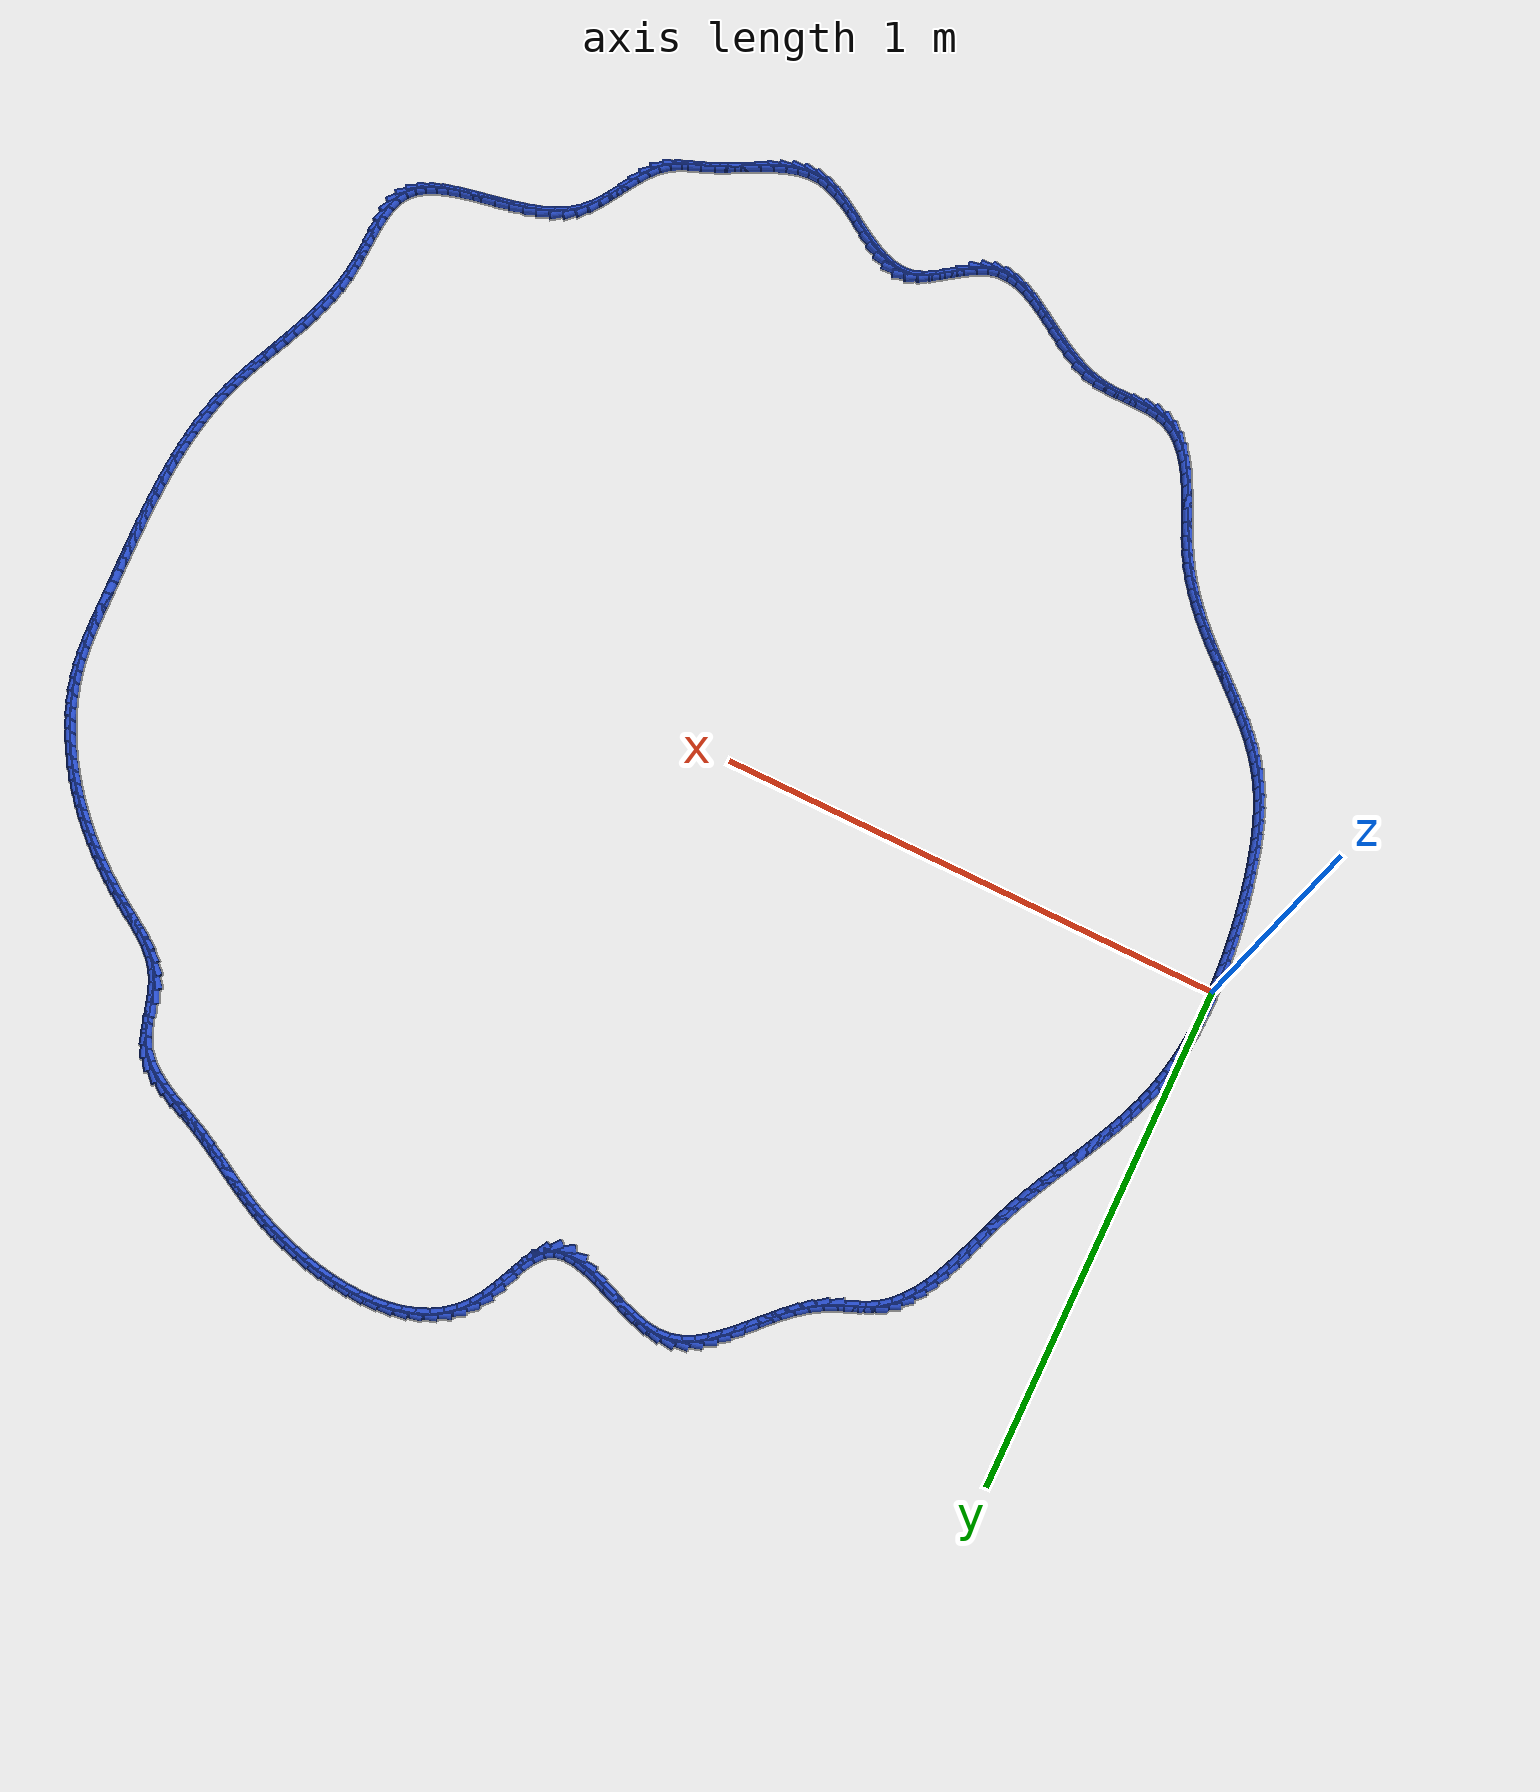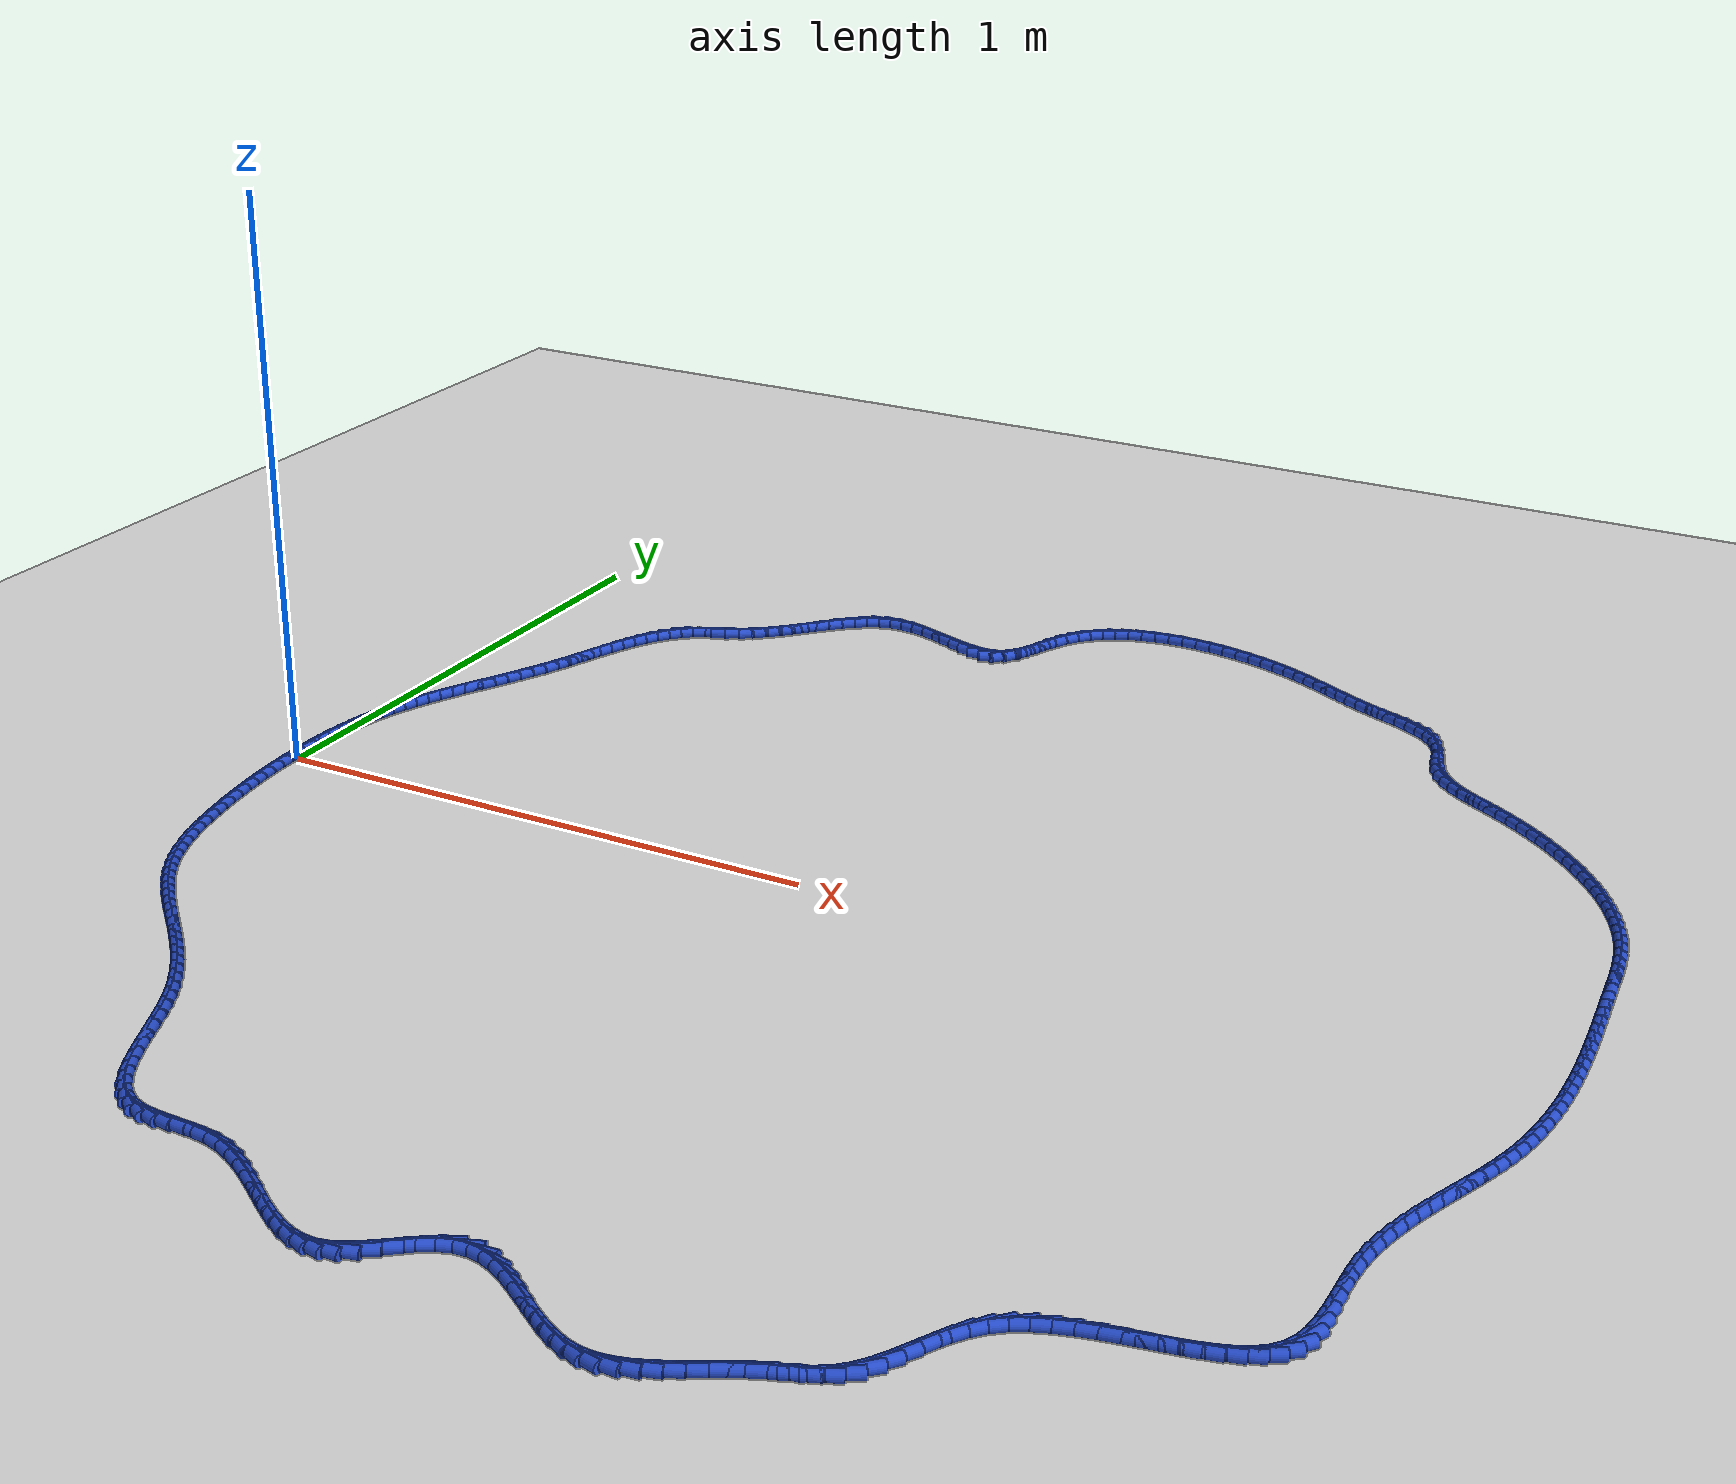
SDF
<sdf version="1.6">
 <world name="default">
  <light name="sun" type="directional">
   <pose>0 0 10 0 -0 0</pose>
   <diffuse>0.8 0.8 0.8 1</diffuse>
   <specular>0.2 0.2 0.2 1</specular>
   <attenuation>
    <range>1000</range>
    <constant>0.9</constant>
    <linear>0.01</linear>
    <quadratic>0.001</quadratic>
   </attenuation>
   <direction>-0.5 0.1 -0.9</direction>
  </light>
  <model name="ground_plane">
   <static>1</static>
   <link name="link">
    <collision name="collision">
     <geometry><plane><normal>0 0 1</normal><size>100 100</size></plane></geometry>
     <surface><friction><ode><mu>100</mu><mu2>50</mu2></ode></friction></surface>
    </collision>
    <visual name="visual">
     <cast_shadows>0</cast_shadows>
     <geometry><plane><normal>0 0 1</normal><size>100 100</size></plane></geometry>
     <material>
      <script><uri>file://media/materials/scripts/gazebo.material</uri><name>Gazebo/WhiteGlow</name></script>
     </material>
    </visual>
   </link>
  </model>
  <gravity>0 0 -9.8</gravity>
  <magnetic_field>6e-06 2.3e-05 -4.2e-05</magnetic_field>
  <atmosphere type="adiabatic"/>
  <physics name="default_physics" default="0" type="ode">
   <max_step_size>0.001</max_step_size>
   <real_time_factor>1</real_time_factor>
   <real_time_update_rate>1000</real_time_update_rate>
  </physics>
  <scene><ambient>0.4 0.4 0.4 1</ambient><background>0.7 0.7 0.7 1</background><shadows>1</shadows></scene>
  <spherical_coordinates>
   <surface_model>EARTH_WGS84</surface_model>
   <latitude_deg>0</latitude_deg>
   <longitude_deg>0</longitude_deg>
   <elevation>0</elevation>
   <heading_deg>0</heading_deg>
  </spherical_coordinates>
  <model name="line">
   <link name="link_0">
    <pose>5.421010862427522e-18 1.3877787807814457e-17 0.01 0 1.57 -1.5659382603258258</pose>
    <collision name="collision">
     <geometry><cylinder><radius>0.01</radius><length>0.08</length></cylinder></geometry>
    </collision>
    <visual name="visual">
     <material>
      <script><name>Gazebo/Blue</name><uri>file://media/materials/scripts/gazebo.material</uri></script>
     </material>
     <geometry><cylinder><radius>0.01</radius><length>0.08</length></cylinder></geometry>
    </visual>
   </link>
   <link name="link_1">
    <pose>-0.00012448770193607386 0.02562474667447096 0.01 0 1.57 1.550838066038636</pose>
    <collision name="collision">
     <geometry><cylinder><radius>0.01</radius><length>0.08</length></cylinder></geometry>
    </collision>
    <visual name="visual">
     <material>
      <script><name>Gazebo/Blue</name><uri>file://media/materials/scripts/gazebo.material</uri></script>
     </material>
     <geometry><cylinder><radius>0.01</radius><length>0.08</length></cylinder></geometry>
    </visual>
   </link>
   <link name="link_2">
    <pose>0.0003884079028893683 0.051319746270860674 0.01 0 1.57 1.523754809734453</pose>
    <collision name="collision">
     <geometry><cylinder><radius>0.01</radius><length>0.08</length></cylinder></geometry>
    </collision>
    <visual name="visual">
     <material>
      <script><name>Gazebo/Blue</name><uri>file://media/materials/scripts/gazebo.material</uri></script>
     </material>
     <geometry><cylinder><radius>0.01</radius><length>0.08</length></cylinder></geometry>
    </visual>
   </link>
   <link name="link_3">
    <pose>0.0015977780576189502 0.07700935037230285 0.01 0 1.57 1.4942167240908684</pose>
    <collision name="collision">
     <geometry><cylinder><radius>0.01</radius><length>0.08</length></cylinder></geometry>
    </collision>
    <visual name="visual">
     <material>
      <script><name>Gazebo/Blue</name><uri>file://media/materials/scripts/gazebo.material</uri></script>
     </material>
     <geometry><cylinder><radius>0.01</radius><length>0.08</length></cylinder></geometry>
    </visual>
   </link>
   <link name="link_4">
    <pose>0.0035627140053952995 0.10261791056193133 0.01 0 1.57 1.4620176359149086</pose>
    <collision name="collision">
     <geometry><cylinder><radius>0.01</radius><length>0.08</length></cylinder></geometry>
    </collision>
    <visual name="visual">
     <material>
      <script><name>Gazebo/Blue</name><uri>file://media/materials/scripts/gazebo.material</uri></script>
     </material>
     <geometry><cylinder><radius>0.01</radius><length>0.08</length></cylinder></geometry>
    </visual>
   </link>
   <link name="link_5">
    <pose>0.006342306989361036 0.12806977842287975 0.01 0 1.57 1.4269354494937865</pose>
    <collision name="collision">
     <geometry><cylinder><radius>0.01</radius><length>0.08</length></cylinder></geometry>
    </collision>
    <visual name="visual">
     <material>
      <script><name>Gazebo/Blue</name><uri>file://media/materials/scripts/gazebo.material</uri></script>
     </material>
     <geometry><cylinder><radius>0.01</radius><length>0.08</length></cylinder></geometry>
    </visual>
   </link>
   <link name="link_6">
    <pose>0.009995648252658779 0.15328930553828193 0.01 0 1.57 1.3887362121927387</pose>
    <collision name="collision">
     <geometry><cylinder><radius>0.01</radius><length>0.08</length></cylinder></geometry>
    </collision>
    <visual name="visual">
     <material>
      <script><name>Gazebo/Blue</name><uri>file://media/materials/scripts/gazebo.material</uri></script>
     </material>
     <geometry><cylinder><radius>0.01</radius><length>0.08</length></cylinder></geometry>
    </visual>
   </link>
   <link name="link_7">
    <pose>0.014581829038431155 0.17820084349127158 0.01 0 1.57 1.34718060379681</pose>
    <collision name="collision">
     <geometry><cylinder><radius>0.01</radius><length>0.08</length></cylinder></geometry>
    </collision>
    <visual name="visual">
     <material>
      <script><name>Gazebo/Blue</name><uri>file://media/materials/scripts/gazebo.material</uri></script>
     </material>
     <geometry><cylinder><radius>0.01</radius><length>0.08</length></cylinder></geometry>
    </visual>
   </link>
   <link name="link_8">
    <pose>0.02015994058982078 0.20272874386498246 0.01 0 1.57 1.30220337523249</pose>
    <collision name="collision">
     <geometry><cylinder><radius>0.01</radius><length>0.08</length></cylinder></geometry>
    </collision>
    <visual name="visual">
     <material>
      <script><name>Gazebo/Blue</name><uri>file://media/materials/scripts/gazebo.material</uri></script>
     </material>
     <geometry><cylinder><radius>0.01</radius><length>0.08</length></cylinder></geometry>
    </visual>
   </link>
   <link name="link_9">
    <pose>0.02678553320749392 0.2268004582328669 0.01 0 1.57 1.2577323411462435</pose>
    <collision name="collision">
     <geometry><cylinder><radius>0.01</radius><length>0.08</length></cylinder></geometry>
    </collision>
    <visual name="visual">
     <material>
      <script><name>Gazebo/Blue</name><uri>file://media/materials/scripts/gazebo.material</uri></script>
     </material>
     <geometry><cylinder><radius>0.01</radius><length>0.08</length></cylinder></geometry>
    </visual>
   </link>
   <link name="link_10">
    <pose>0.03443036054978534 0.2504167996481787 0.01 0 1.57 1.2181870109696322</pose>
    <collision name="collision">
     <geometry><cylinder><radius>0.01</radius><length>0.08</length></cylinder></geometry>
    </collision>
    <visual name="visual">
     <material>
      <script><name>Gazebo/Blue</name><uri>file://media/materials/scripts/gazebo.material</uri></script>
     </material>
     <geometry><cylinder><radius>0.01</radius><length>0.08</length></cylinder></geometry>
    </visual>
   </link>
   <link name="link_11">
    <pose>0.042981050054630425 0.2736531066502133 0.01 0 1.57 1.184088666032764</pose>
    <collision name="collision">
     <geometry><cylinder><radius>0.01</radius><length>0.08</length></cylinder></geometry>
    </collision>
    <visual name="visual">
     <material>
      <script><name>Gazebo/Blue</name><uri>file://media/materials/scripts/gazebo.material</uri></script>
     </material>
     <geometry><cylinder><radius>0.01</radius><length>0.08</length></cylinder></geometry>
    </visual>
   </link>
   <link name="link_12">
    <pose>0.05232042228121659 0.29658805058791815 0.01 0 1.57 1.15564467206756</pose>
    <collision name="collision">
     <geometry><cylinder><radius>0.01</radius><length>0.08</length></cylinder></geometry>
    </collision>
    <visual name="visual">
     <material>
      <script><name>Gazebo/Blue</name><uri>file://media/materials/scripts/gazebo.material</uri></script>
     </material>
     <geometry><cylinder><radius>0.01</radius><length>0.08</length></cylinder></geometry>
    </visual>
   </link>
   <link name="link_13">
    <pose>0.06233129778873132 0.3193003028102408 0.01 0 1.57 1.1329560969378643</pose>
    <collision name="collision">
     <geometry><cylinder><radius>0.01</radius><length>0.08</length></cylinder></geometry>
    </collision>
    <visual name="visual">
     <material>
      <script><name>Gazebo/Blue</name><uri>file://media/materials/scripts/gazebo.material</uri></script>
     </material>
     <geometry><cylinder><radius>0.01</radius><length>0.08</length></cylinder></geometry>
    </visual>
   </link>
   <link name="link_14">
    <pose>0.072896497136362 0.3418685346661286 0.01 0 1.57 1.1160435405415503</pose>
    <collision name="collision">
     <geometry><cylinder><radius>0.01</radius><length>0.08</length></cylinder></geometry>
    </collision>
    <visual name="visual">
     <material>
      <script><name>Gazebo/Blue</name><uri>file://media/materials/scripts/gazebo.material</uri></script>
     </material>
     <geometry><cylinder><radius>0.01</radius><length>0.08</length></cylinder></geometry>
    </visual>
   </link>
   <link name="link_15">
    <pose>0.08389884088329615 0.3643714175045291 0.01 0 1.57 1.1048700795377384</pose>
    <collision name="collision">
     <geometry><cylinder><radius>0.01</radius><length>0.08</length></cylinder></geometry>
    </collision>
    <visual name="visual">
     <material>
      <script><name>Gazebo/Blue</name><uri>file://media/materials/scripts/gazebo.material</uri></script>
     </material>
     <geometry><cylinder><radius>0.01</radius><length>0.08</length></cylinder></geometry>
    </visual>
   </link>
   <link name="link_16">
    <pose>0.09522114958872116 0.3868876226743898 0.01 0 1.57 1.0993593445898155</pose>
    <collision name="collision">
     <geometry><cylinder><radius>0.01</radius><length>0.08</length></cylinder></geometry>
    </collision>
    <visual name="visual">
     <material>
      <script><name>Gazebo/Blue</name><uri>file://media/materials/scripts/gazebo.material</uri></script>
     </material>
     <geometry><cylinder><radius>0.01</radius><length>0.08</length></cylinder></geometry>
    </visual>
   </link>
   <link name="link_17">
    <pose>0.10674624381182446 0.4094958215246581 0.01 0 1.57 1.0994079437964333</pose>
    <collision name="collision">
     <geometry><cylinder><radius>0.01</radius><length>0.08</length></cylinder></geometry>
    </collision>
    <visual name="visual">
     <material>
      <script><name>Gazebo/Blue</name><uri>file://media/materials/scripts/gazebo.material</uri></script>
     </material>
     <geometry><cylinder><radius>0.01</radius><length>0.08</length></cylinder></geometry>
    </visual>
   </link>
   <link name="link_18">
    <pose>0.11835694411179348 0.4322746854042813 0.01 0 1.57 1.1048922381688164</pose>
    <collision name="collision">
     <geometry><cylinder><radius>0.01</radius><length>0.08</length></cylinder></geometry>
    </collision>
    <visual name="visual">
     <material>
      <script><name>Gazebo/Blue</name><uri>file://media/materials/scripts/gazebo.material</uri></script>
     </material>
     <geometry><cylinder><radius>0.01</radius><length>0.08</length></cylinder></geometry>
    </visual>
   </link>
   <link name="link_19">
    <pose>0.12993607104781574 0.45530288566220734 0.01 0 1.57 1.1156699416593707</pose>
    <collision name="collision">
     <geometry><cylinder><radius>0.01</radius><length>0.08</length></cylinder></geometry>
    </collision>
    <visual name="visual">
     <material>
      <script><name>Gazebo/Blue</name><uri>file://media/materials/scripts/gazebo.material</uri></script>
     </material>
     <geometry><cylinder><radius>0.01</radius><length>0.08</length></cylinder></geometry>
    </visual>
   </link>
   <link name="link_20">
    <pose>0.14136644517907868 0.4786590936473834 0.01 0 1.57 1.1315772874365169</pose>
    <collision name="collision">
     <geometry><cylinder><radius>0.01</radius><length>0.08</length></cylinder></geometry>
    </collision>
    <visual name="visual">
     <material>
      <script><name>Gazebo/Blue</name><uri>file://media/materials/scripts/gazebo.material</uri></script>
     </material>
     <geometry><cylinder><radius>0.01</radius><length>0.08</length></cylinder></geometry>
    </visual>
   </link>
   <link name="link_21">
    <pose>0.15253088706476967 0.502421980708757 0.01 0 1.57 1.1524226938475504</pose>
    <collision name="collision">
     <geometry><cylinder><radius>0.01</radius><length>0.08</length></cylinder></geometry>
    </collision>
    <visual name="visual">
     <material>
      <script><name>Gazebo/Blue</name><uri>file://media/materials/scripts/gazebo.material</uri></script>
     </material>
     <geometry><cylinder><radius>0.01</radius><length>0.08</length></cylinder></geometry>
    </visual>
   </link>
   <link name="link_22">
    <pose>0.16331221726407616 0.5266702181952754 0.01 0 1.57 1.1779779294163575</pose>
    <collision name="collision">
     <geometry><cylinder><radius>0.01</radius><length>0.08</length></cylinder></geometry>
    </collision>
    <visual name="visual">
     <material>
      <script><name>Gazebo/Blue</name><uri>file://media/materials/scripts/gazebo.material</uri></script>
     </material>
     <geometry><cylinder><radius>0.01</radius><length>0.08</length></cylinder></geometry>
    </visual>
   </link>
   <link name="link_23">
    <pose>0.1735932590599459 0.5514824747864997 0.01 0 1.57 1.204589698787398</pose>
    <collision name="collision">
     <geometry><cylinder><radius>0.01</radius><length>0.08</length></cylinder></geometry>
    </collision>
    <visual name="visual">
     <material>
      <script><name>Gazebo/Blue</name><uri>file://media/materials/scripts/gazebo.material</uri></script>
     </material>
     <geometry><cylinder><radius>0.01</radius><length>0.08</length></cylinder></geometry>
    </visual>
   </link>
   <link name="link_24">
    <pose>0.18332845318040278 0.576867231397506 0.01 0 1.57 1.2202474084535286</pose>
    <collision name="collision">
     <geometry><cylinder><radius>0.01</radius><length>0.08</length></cylinder></geometry>
    </collision>
    <visual name="visual">
     <material>
      <script><name>Gazebo/Blue</name><uri>file://media/materials/scripts/gazebo.material</uri></script>
     </material>
     <geometry><cylinder><radius>0.01</radius><length>0.08</length></cylinder></geometry>
    </visual>
   </link>
   <link name="link_25">
    <pose>0.1927303491308902 0.6025800127249246 0.01 0 1.57 1.2227287700935614</pose>
    <collision name="collision">
     <geometry><cylinder><radius>0.01</radius><length>0.08</length></cylinder></geometry>
    </collision>
    <visual name="visual">
     <material>
      <script><name>Gazebo/Blue</name><uri>file://media/materials/scripts/gazebo.material</uri></script>
     </material>
     <geometry><cylinder><radius>0.01</radius><length>0.08</length></cylinder></geometry>
    </visual>
   </link>
   <link name="link_26">
    <pose>0.20206962284783564 0.6283193773973579 0.01 0 1.57 1.2120897841946021</pose>
    <collision name="collision">
     <geometry><cylinder><radius>0.01</radius><length>0.08</length></cylinder></geometry>
    </collision>
    <visual name="visual">
     <material>
      <script><name>Gazebo/Blue</name><uri>file://media/materials/scripts/gazebo.material</uri></script>
     </material>
     <geometry><cylinder><radius>0.01</radius><length>0.08</length></cylinder></geometry>
    </visual>
   </link>
   <link name="link_27">
    <pose>0.2116169502676666 0.653783884043408 0.01 0 1.57 1.1878409056218606</pose>
    <collision name="collision">
     <geometry><cylinder><radius>0.01</radius><length>0.08</length></cylinder></geometry>
    </collision>
    <visual name="visual">
     <material>
      <script><name>Gazebo/Blue</name><uri>file://media/materials/scripts/gazebo.material</uri></script>
     </material>
     <geometry><cylinder><radius>0.01</radius><length>0.08</length></cylinder></geometry>
    </visual>
   </link>
   <link name="link_28">
    <pose>0.22164300732681036 0.6786720912916773 0.01 0 1.57 1.1489558398082087</pose>
    <collision name="collision">
     <geometry><cylinder><radius>0.01</radius><length>0.08</length></cylinder></geometry>
    </collision>
    <visual name="visual">
     <material>
      <script><name>Gazebo/Blue</name><uri>file://media/materials/scripts/gazebo.material</uri></script>
     </material>
     <geometry><cylinder><radius>0.01</radius><length>0.08</length></cylinder></geometry>
    </visual>
   </link>
   <link name="link_29">
    <pose>0.23241846996169443 0.7026825577707675 0.01 0 1.57 1.0939258736134703</pose>
    <collision name="collision">
     <geometry><cylinder><radius>0.01</radius><length>0.08</length></cylinder></geometry>
    </collision>
    <visual name="visual">
     <material>
      <script><name>Gazebo/Blue</name><uri>file://media/materials/scripts/gazebo.material</uri></script>
     </material>
     <geometry><cylinder><radius>0.01</radius><length>0.08</length></cylinder></geometry>
    </visual>
   </link>
   <link name="link_30">
    <pose>0.24421401410874602 0.7255138421092808 0.01 0 1.57 1.0209290929186816</pose>
    <collision name="collision">
     <geometry><cylinder><radius>0.01</radius><length>0.08</length></cylinder></geometry>
    </collision>
    <visual name="visual">
     <material>
      <script><name>Gazebo/Blue</name><uri>file://media/materials/scripts/gazebo.material</uri></script>
     </material>
     <geometry><cylinder><radius>0.01</radius><length>0.08</length></cylinder></geometry>
    </visual>
   </link>
   <link name="link_31">
    <pose>0.2573003157043927 0.7468645029358196 0.01 0 1.57 0.9282349180417167</pose>
    <collision name="collision">
     <geometry><cylinder><radius>0.01</radius><length>0.08</length></cylinder></geometry>
    </collision>
    <visual name="visual">
     <material>
      <script><name>Gazebo/Blue</name><uri>file://media/materials/scripts/gazebo.material</uri></script>
     </material>
     <geometry><cylinder><radius>0.01</radius><length>0.08</length></cylinder></geometry>
    </visual>
   </link>
   <link name="link_32">
    <pose>0.2719480506850618 0.7664330988789856 0.01 0 1.57 0.814986091452604</pose>
    <collision name="collision">
     <geometry><cylinder><radius>0.01</radius><length>0.08</length></cylinder></geometry>
    </collision>
    <visual name="visual">
     <material>
      <script><name>Gazebo/Blue</name><uri>file://media/materials/scripts/gazebo.material</uri></script>
     </material>
     <geometry><cylinder><radius>0.01</radius><length>0.08</length></cylinder></geometry>
    </visual>
   </link>
   <link name="link_33">
    <pose>0.2884278949871807 0.7839181885673814 0.01 0 1.57 0.6823734579431204</pose>
    <collision name="collision">
     <geometry><cylinder><radius>0.01</radius><length>0.08</length></cylinder></geometry>
    </collision>
    <visual name="visual">
     <material>
      <script><name>Gazebo/Blue</name><uri>file://media/materials/scripts/gazebo.material</uri></script>
     </material>
     <geometry><cylinder><radius>0.01</radius><length>0.08</length></cylinder></geometry>
    </visual>
   </link>
   <link name="link_34">
    <pose>0.3070105245471767 0.7990183306296086 0.01 0 1.57 0.5382947942533804</pose>
    <collision name="collision">
     <geometry><cylinder><radius>0.01</radius><length>0.08</length></cylinder></geometry>
    </collision>
    <visual name="visual">
     <material>
      <script><name>Gazebo/Blue</name><uri>file://media/materials/scripts/gazebo.material</uri></script>
     </material>
     <geometry><cylinder><radius>0.01</radius><length>0.08</length></cylinder></geometry>
    </visual>
   </link>
   <link name="link_35">
    <pose>0.32791731947973674 0.8115020721369399 0.01 0 1.57 0.43880305395550334</pose>
    <collision name="collision">
     <geometry><cylinder><radius>0.01</radius><length>0.08</length></cylinder></geometry>
    </collision>
    <visual name="visual">
     <material>
      <script><name>Gazebo/Blue</name><uri>file://media/materials/scripts/gazebo.material</uri></script>
     </material>
     <geometry><cylinder><radius>0.01</radius><length>0.08</length></cylinder></geometry>
    </visual>
   </link>
   <link name="link_36">
    <pose>0.35064404672669786 0.8221681597628778 0.01 0 1.57 0.4179271606563806</pose>
    <collision name="collision">
     <geometry><cylinder><radius>0.01</radius><length>0.08</length></cylinder></geometry>
    </collision>
    <visual name="visual">
     <material>
      <script><name>Gazebo/Blue</name><uri>file://media/materials/scripts/gazebo.material</uri></script>
     </material>
     <geometry><cylinder><radius>0.01</radius><length>0.08</length></cylinder></geometry>
    </visual>
   </link>
   <link name="link_37">
    <pose>0.37413396841889707 0.8325997667291463 0.01 0 1.57 0.4708246415328438</pose>
    <collision name="collision">
     <geometry><cylinder><radius>0.01</radius><length>0.08</length></cylinder></geometry>
    </collision>
    <visual name="visual">
     <material>
      <script><name>Gazebo/Blue</name><uri>file://media/materials/scripts/gazebo.material</uri></script>
     </material>
     <geometry><cylinder><radius>0.01</radius><length>0.08</length></cylinder></geometry>
    </visual>
   </link>
   <link name="link_38">
    <pose>0.39731648077785475 0.8443997525790474 0.01 0 1.57 0.5822093859039558</pose>
    <collision name="collision">
     <geometry><cylinder><radius>0.01</radius><length>0.08</length></cylinder></geometry>
    </collision>
    <visual name="visual">
     <material>
      <script><name>Gazebo/Blue</name><uri>file://media/materials/scripts/gazebo.material</uri></script>
     </material>
     <geometry><cylinder><radius>0.01</radius><length>0.08</length></cylinder></geometry>
    </visual>
   </link>
   <link name="link_39">
    <pose>0.41929680986111373 0.8588700799174293 0.01 0 1.57 0.6832533506091669</pose>
    <collision name="collision">
     <geometry><cylinder><radius>0.01</radius><length>0.08</length></cylinder></geometry>
    </collision>
    <visual name="visual">
     <material>
      <script><name>Gazebo/Blue</name><uri>file://media/materials/scripts/gazebo.material</uri></script>
     </material>
     <geometry><cylinder><radius>0.01</radius><length>0.08</length></cylinder></geometry>
    </visual>
   </link>
   <link name="link_40">
    <pose>0.44007369854116846 0.8757836393772874 0.01 0 1.57 0.7539764289823443</pose>
    <collision name="collision">
     <geometry><cylinder><radius>0.01</radius><length>0.08</length></cylinder></geometry>
    </collision>
    <visual name="visual">
     <material>
      <script><name>Gazebo/Blue</name><uri>file://media/materials/scripts/gazebo.material</uri></script>
     </material>
     <geometry><cylinder><radius>0.01</radius><length>0.08</length></cylinder></geometry>
    </visual>
   </link>
   <link name="link_41">
    <pose>0.4599290167788269 0.8944288072680271 0.01 0 1.57 0.7969516579210766</pose>
    <collision name="collision">
     <geometry><cylinder><radius>0.01</radius><length>0.08</length></cylinder></geometry>
    </collision>
    <visual name="visual">
     <material>
      <script><name>Gazebo/Blue</name><uri>file://media/materials/scripts/gazebo.material</uri></script>
     </material>
     <geometry><cylinder><radius>0.01</radius><length>0.08</length></cylinder></geometry>
    </visual>
   </link>
   <link name="link_42">
    <pose>0.47914474778315613 0.9140937660977345 0.01 0 1.57 0.8140993935547778</pose>
    <collision name="collision">
     <geometry><cylinder><radius>0.01</radius><length>0.08</length></cylinder></geometry>
    </collision>
    <visual name="visual">
     <material>
      <script><name>Gazebo/Blue</name><uri>file://media/materials/scripts/gazebo.material</uri></script>
     </material>
     <geometry><cylinder><radius>0.01</radius><length>0.08</length></cylinder></geometry>
    </visual>
   </link>
   <link name="link_43">
    <pose>0.4980028747632227 0.9340666983744943 0.01 0 1.57 0.8059050501442396</pose>
    <collision name="collision">
     <geometry><cylinder><radius>0.01</radius><length>0.08</length></cylinder></geometry>
    </collision>
    <visual name="visual">
     <material>
      <script><name>Gazebo/Blue</name><uri>file://media/materials/scripts/gazebo.material</uri></script>
     </material>
     <geometry><cylinder><radius>0.01</radius><length>0.08</length></cylinder></geometry>
    </visual>
   </link>
   <link name="link_44">
    <pose>0.5167853809280936 0.9536357866063925 0.01 0 1.57 0.7710986829664985</pose>
    <collision name="collision">
     <geometry><cylinder><radius>0.01</radius><length>0.08</length></cylinder></geometry>
    </collision>
    <visual name="visual">
     <material>
      <script><name>Gazebo/Blue</name><uri>file://media/materials/scripts/gazebo.material</uri></script>
     </material>
     <geometry><cylinder><radius>0.01</radius><length>0.08</length></cylinder></geometry>
    </visual>
   </link>
   <link name="link_45">
    <pose>0.5357742494868358 0.9720892133015147 0.01 0 1.57 0.706586211054229</pose>
    <collision name="collision">
     <geometry><cylinder><radius>0.01</radius><length>0.08</length></cylinder></geometry>
    </collision>
    <visual name="visual">
     <material>
      <script><name>Gazebo/Blue</name><uri>file://media/materials/scripts/gazebo.material</uri></script>
     </material>
     <geometry><cylinder><radius>0.01</radius><length>0.08</length></cylinder></geometry>
    </visual>
   </link>
   <link name="link_46">
    <pose>0.5552514636485159 0.9887151609679462 0.01 0 1.57 0.6078487183160051</pose>
    <collision name="collision">
     <geometry><cylinder><radius>0.01</radius><length>0.08</length></cylinder></geometry>
    </collision>
    <visual name="visual">
     <material>
      <script><name>Gazebo/Blue</name><uri>file://media/materials/scripts/gazebo.material</uri></script>
     </material>
     <geometry><cylinder><radius>0.01</radius><length>0.08</length></cylinder></geometry>
    </visual>
   </link>
   <link name="link_47">
    <pose>0.5754990066222009 1.002801812113773 0.01 0 1.57 0.47059458351835903</pose>
    <collision name="collision">
     <geometry><cylinder><radius>0.01</radius><length>0.08</length></cylinder></geometry>
    </collision>
    <visual name="visual">
     <material>
      <script><name>Gazebo/Blue</name><uri>file://media/materials/scripts/gazebo.material</uri></script>
     </material>
     <geometry><cylinder><radius>0.01</radius><length>0.08</length></cylinder></geometry>
    </visual>
   </link>
   <link name="link_48">
    <pose>0.5967988616169575 1.01363734924708 0.01 0 1.57 0.2947917670698464</pose>
    <collision name="collision">
     <geometry><cylinder><radius>0.01</radius><length>0.08</length></cylinder></geometry>
    </collision>
    <visual name="visual">
     <material>
      <script><name>Gazebo/Blue</name><uri>file://media/materials/scripts/gazebo.material</uri></script>
     </material>
     <geometry><cylinder><radius>0.01</radius><length>0.08</length></cylinder></geometry>
    </visual>
   </link>
   <link name="link_49">
    <pose>0.6194330118418525 1.020509954875953 0.01 0 1.57 0.09048260221825627</pose>
    <collision name="collision">
     <geometry><cylinder><radius>0.01</radius><length>0.08</length></cylinder></geometry>
    </collision>
    <visual name="visual">
     <material>
      <script><name>Gazebo/Blue</name><uri>file://media/materials/scripts/gazebo.material</uri></script>
     </material>
     <geometry><cylinder><radius>0.01</radius><length>0.08</length></cylinder></geometry>
    </visual>
   </link>
   <link name="link_50">
    <pose>0.6436824839115431 1.022710117809935 0.01 0 1.57 -0.10090945656496318</pose>
    <collision name="collision">
     <geometry><cylinder><radius>0.01</radius><length>0.08</length></cylinder></geometry>
    </collision>
    <visual name="visual">
     <material>
      <script><name>Gazebo/Blue</name><uri>file://media/materials/scripts/gazebo.material</uri></script>
     </material>
     <geometry><cylinder><radius>0.01</radius><length>0.08</length></cylinder></geometry>
    </visual>
   </link>
   <link name="link_51">
    <pose>0.6695969153876722 1.0200861943360138 0.01 0 1.57 -0.22910706704701023</pose>
    <collision name="collision">
     <geometry><cylinder><radius>0.01</radius><length>0.08</length></cylinder></geometry>
    </collision>
    <visual name="visual">
     <material>
      <script><name>Gazebo/Blue</name><uri>file://media/materials/scripts/gazebo.material</uri></script>
     </material>
     <geometry><cylinder><radius>0.01</radius><length>0.08</length></cylinder></geometry>
    </visual>
   </link>
   <link name="link_52">
    <pose>0.6966948825329233 1.0137669030718892 0.01 0 1.57 -0.3042871475545219</pose>
    <collision name="collision">
     <geometry><cylinder><radius>0.01</radius><length>0.08</length></cylinder></geometry>
    </collision>
    <visual name="visual">
     <material>
      <script><name>Gazebo/Blue</name><uri>file://media/materials/scripts/gazebo.material</uri></script>
     </material>
     <geometry><cylinder><radius>0.01</radius><length>0.08</length></cylinder></geometry>
    </visual>
   </link>
   <link name="link_53">
    <pose>0.7244207541022027 1.0050598732389897 0.01 0 1.57 -0.33852561083776095</pose>
    <collision name="collision">
     <geometry><cylinder><radius>0.01</radius><length>0.08</length></cylinder></geometry>
    </collision>
    <visual name="visual">
     <material>
      <script><name>Gazebo/Blue</name><uri>file://media/materials/scripts/gazebo.material</uri></script>
     </material>
     <geometry><cylinder><radius>0.01</radius><length>0.08</length></cylinder></geometry>
    </visual>
   </link>
   <link name="link_54">
    <pose>0.7522188988504166 0.9952727340587431 0.01 0 1.57 -0.3366566843344308</pose>
    <collision name="collision">
     <geometry><cylinder><radius>0.01</radius><length>0.08</length></cylinder></geometry>
    </collision>
    <visual name="visual">
     <material>
      <script><name>Gazebo/Blue</name><uri>file://media/materials/scripts/gazebo.material</uri></script>
     </material>
     <geometry><cylinder><radius>0.01</radius><length>0.08</length></cylinder></geometry>
    </visual>
   </link>
   <link name="link_55">
    <pose>0.7795336855324717 0.9857131147525774 0.01 0 1.57 -0.29639801965976714</pose>
    <collision name="collision">
     <geometry><cylinder><radius>0.01</radius><length>0.08</length></cylinder></geometry>
    </collision>
    <visual name="visual">
     <material>
      <script><name>Gazebo/Blue</name><uri>file://media/materials/scripts/gazebo.material</uri></script>
     </material>
     <geometry><cylinder><radius>0.01</radius><length>0.08</length></cylinder></geometry>
    </visual>
   </link>
   <link name="link_56">
    <pose>0.8058094829032749 0.9776886445419211 0.01 0 1.57 -0.20693960312782025</pose>
    <collision name="collision">
     <geometry><cylinder><radius>0.01</radius><length>0.08</length></cylinder></geometry>
    </collision>
    <visual name="visual">
     <material>
      <script><name>Gazebo/Blue</name><uri>file://media/materials/scripts/gazebo.material</uri></script>
     </material>
     <geometry><cylinder><radius>0.01</radius><length>0.08</length></cylinder></geometry>
    </visual>
   </link>
   <link name="link_57">
    <pose>0.8304906597177322 0.9725069526482022 0.01 0 1.57 -0.045740024165443136</pose>
    <collision name="collision">
     <geometry><cylinder><radius>0.01</radius><length>0.08</length></cylinder></geometry>
    </collision>
    <visual name="visual">
     <material>
      <script><name>Gazebo/Blue</name><uri>file://media/materials/scripts/gazebo.material</uri></script>
     </material>
     <geometry><cylinder><radius>0.01</radius><length>0.08</length></cylinder></geometry>
    </visual>
   </link>
   <link name="link_58">
    <pose>0.8530215847307502 0.971475668292849 0.01 0 1.57 0.2196871473846764</pose>
    <collision name="collision">
     <geometry><cylinder><radius>0.01</radius><length>0.08</length></cylinder></geometry>
    </collision>
    <visual name="visual">
     <material>
      <script><name>Gazebo/Blue</name><uri>file://media/materials/scripts/gazebo.material</uri></script>
     </material>
     <geometry><cylinder><radius>0.01</radius><length>0.08</length></cylinder></geometry>
    </visual>
   </link>
   <link name="link_59">
    <pose>0.8728466266972352 0.9759024206972896 0.01 0 1.57 0.5904128418060222</pose>
    <collision name="collision">
     <geometry><cylinder><radius>0.01</radius><length>0.08</length></cylinder></geometry>
    </collision>
    <visual name="visual">
     <material>
      <script><name>Gazebo/Blue</name><uri>file://media/materials/scripts/gazebo.material</uri></script>
     </material>
     <geometry><cylinder><radius>0.01</radius><length>0.08</length></cylinder></geometry>
    </visual>
   </link>
   <link name="link_60">
    <pose>0.8894455877368677 0.9870262763817774 0.01 0 1.57 0.9096011142544163</pose>
    <collision name="collision">
     <geometry><cylinder><radius>0.01</radius><length>0.08</length></cylinder></geometry>
    </collision>
    <visual name="visual">
     <material>
      <script><name>Gazebo/Blue</name><uri>file://media/materials/scripts/gazebo.material</uri></script>
     </material>
     <geometry><cylinder><radius>0.01</radius><length>0.08</length></cylinder></geometry>
    </visual>
   </link>
   <link name="link_61">
    <pose>0.9030871226602335 1.0045598910482978 0.01 0 1.57 1.0839991079166227</pose>
    <collision name="collision">
     <geometry><cylinder><radius>0.01</radius><length>0.08</length></cylinder></geometry>
    </collision>
    <visual name="visual">
     <material>
      <script><name>Gazebo/Blue</name><uri>file://media/materials/scripts/gazebo.material</uri></script>
     </material>
     <geometry><cylinder><radius>0.01</radius><length>0.08</length></cylinder></geometry>
    </visual>
   </link>
   <link name="link_62">
    <pose>0.9148144979090209 1.026717065685785 0.01 0 1.57 1.1590074510101607</pose>
    <collision name="collision">
     <geometry><cylinder><radius>0.01</radius><length>0.08</length></cylinder></geometry>
    </collision>
    <visual name="visual">
     <material>
      <script><name>Gazebo/Blue</name><uri>file://media/materials/scripts/gazebo.material</uri></script>
     </material>
     <geometry><cylinder><radius>0.01</radius><length>0.08</length></cylinder></geometry>
    </visual>
   </link>
   <link name="link_63">
    <pose>0.9257035647813951 1.0516485503764412 0.01 0 1.57 1.1644275357256617</pose>
    <collision name="collision">
     <geometry><cylinder><radius>0.01</radius><length>0.08</length></cylinder></geometry>
    </collision>
    <visual name="visual">
     <material>
      <script><name>Gazebo/Blue</name><uri>file://media/materials/scripts/gazebo.material</uri></script>
     </material>
     <geometry><cylinder><radius>0.01</radius><length>0.08</length></cylinder></geometry>
    </visual>
   </link>
   <link name="link_64">
    <pose>0.9368301745755226 1.0775050952024687 0.01 0 1.57 1.1079888950414456</pose>
    <collision name="collision">
     <geometry><cylinder><radius>0.01</radius><length>0.08</length></cylinder></geometry>
    </collision>
    <visual name="visual">
     <material>
      <script><name>Gazebo/Blue</name><uri>file://media/materials/scripts/gazebo.material</uri></script>
     </material>
     <geometry><cylinder><radius>0.01</radius><length>0.08</length></cylinder></geometry>
    </visual>
   </link>
   <link name="link_65">
    <pose>0.9492701785895689 1.1024374502460692 0.01 0 1.57 0.9866092341428063</pose>
    <collision name="collision">
     <geometry><cylinder><radius>0.01</radius><length>0.08</length></cylinder></geometry>
    </collision>
    <visual name="visual">
     <material>
      <script><name>Gazebo/Blue</name><uri>file://media/materials/scripts/gazebo.material</uri></script>
     </material>
     <geometry><cylinder><radius>0.01</radius><length>0.08</length></cylinder></geometry>
    </visual>
   </link>
   <link name="link_66">
    <pose>0.9640104831739069 1.1247317459999717 0.01 0 1.57 0.8384691981079193</pose>
    <collision name="collision">
     <geometry><cylinder><radius>0.01</radius><length>0.08</length></cylinder></geometry>
    </collision>
    <visual name="visual">
     <material>
      <script><name>Gazebo/Blue</name><uri>file://media/materials/scripts/gazebo.material</uri></script>
     </material>
     <geometry><cylinder><radius>0.01</radius><length>0.08</length></cylinder></geometry>
    </visual>
   </link>
   <link name="link_67">
    <pose>0.9812378231117642 1.1438920298587738 0.01 0 1.57 0.6930118332962242</pose>
    <collision name="collision">
     <geometry><cylinder><radius>0.01</radius><length>0.08</length></cylinder></geometry>
    </collision>
    <visual name="visual">
     <material>
      <script><name>Gazebo/Blue</name><uri>file://media/materials/scripts/gazebo.material</uri></script>
     </material>
     <geometry><cylinder><radius>0.01</radius><length>0.08</length></cylinder></geometry>
    </visual>
   </link>
   <link name="link_68">
    <pose>1.000715633570668 1.1600666407386453 0.01 0 1.57 0.5556899170895744</pose>
    <collision name="collision">
     <geometry><cylinder><radius>0.01</radius><length>0.08</length></cylinder></geometry>
    </collision>
    <visual name="visual">
     <material>
      <script><name>Gazebo/Blue</name><uri>file://media/materials/scripts/gazebo.material</uri></script>
     </material>
     <geometry><cylinder><radius>0.01</radius><length>0.08</length></cylinder></geometry>
    </visual>
   </link>
   <link name="link_69">
    <pose>1.0222034998393403 1.1734097773396532 0.01 0 1.57 0.42998149815365205</pose>
    <collision name="collision">
     <geometry><cylinder><radius>0.01</radius><length>0.08</length></cylinder></geometry>
    </collision>
    <visual name="visual">
     <material>
      <script><name>Gazebo/Blue</name><uri>file://media/materials/scripts/gazebo.material</uri></script>
     </material>
     <geometry><cylinder><radius>0.01</radius><length>0.08</length></cylinder></geometry>
    </visual>
   </link>
   <link name="link_70">
    <pose>1.0454610072065047 1.1840756383618658 0.01 0 1.57 0.3174067228604865</pose>
    <collision name="collision">
     <geometry><cylinder><radius>0.01</radius><length>0.08</length></cylinder></geometry>
    </collision>
    <visual name="visual">
     <material>
      <script><name>Gazebo/Blue</name><uri>file://media/materials/scripts/gazebo.material</uri></script>
     </material>
     <geometry><cylinder><radius>0.01</radius><length>0.08</length></cylinder></geometry>
    </visual>
   </link>
   <link name="link_71">
    <pose>1.070247740960885 1.1922184225053516 0.01 0 1.57 0.2179138028654509</pose>
    <collision name="collision">
     <geometry><cylinder><radius>0.01</radius><length>0.08</length></cylinder></geometry>
    </collision>
    <visual name="visual">
     <material>
      <script><name>Gazebo/Blue</name><uri>file://media/materials/scripts/gazebo.material</uri></script>
     </material>
     <geometry><cylinder><radius>0.01</radius><length>0.08</length></cylinder></geometry>
    </visual>
   </link>
   <link name="link_72">
    <pose>1.0963232863912042 1.1979923284701777 0.01 0 1.57 0.13047536613558755</pose>
    <collision name="collision">
     <geometry><cylinder><radius>0.01</radius><length>0.08</length></cylinder></geometry>
    </collision>
    <visual name="visual">
     <material>
      <script><name>Gazebo/Blue</name><uri>file://media/materials/scripts/gazebo.material</uri></script>
     </material>
     <geometry><cylinder><radius>0.01</radius><length>0.08</length></cylinder></geometry>
    </visual>
   </link>
   <link name="link_73">
    <pose>1.1234472287861852 1.201551554956412 0.01 0 1.57 0.05360568125429907</pose>
    <collision name="collision">
     <geometry><cylinder><radius>0.01</radius><length>0.08</length></cylinder></geometry>
    </collision>
    <visual name="visual">
     <material>
      <script><name>Gazebo/Blue</name><uri>file://media/materials/scripts/gazebo.material</uri></script>
     </material>
     <geometry><cylinder><radius>0.01</radius><length>0.08</length></cylinder></geometry>
    </visual>
   </link>
   <link name="link_74">
    <pose>1.151379153434551 1.2030503006641227 0.01 0 1.57 -0.014298802001797738</pose>
    <collision name="collision">
     <geometry><cylinder><radius>0.01</radius><length>0.08</length></cylinder></geometry>
    </collision>
    <visual name="visual">
     <material>
      <script><name>Gazebo/Blue</name><uri>file://media/materials/scripts/gazebo.material</uri></script>
     </material>
     <geometry><cylinder><radius>0.01</radius><length>0.08</length></cylinder></geometry>
    </visual>
   </link>
   <link name="link_75">
    <pose>1.1798786456250254 1.2026427642933775 0.01 0 1.57 -0.07477779386527697</pose>
    <collision name="collision">
     <geometry><cylinder><radius>0.01</radius><length>0.08</length></cylinder></geometry>
    </collision>
    <visual name="visual">
     <material>
      <script><name>Gazebo/Blue</name><uri>file://media/materials/scripts/gazebo.material</uri></script>
     </material>
     <geometry><cylinder><radius>0.01</radius><length>0.08</length></cylinder></geometry>
    </visual>
   </link>
   <link name="link_76">
    <pose>1.2087052906463314 1.2004831445442443 0.01 0 1.57 -0.12923298694747284</pose>
    <collision name="collision">
     <geometry><cylinder><radius>0.01</radius><length>0.08</length></cylinder></geometry>
    </collision>
    <visual name="visual">
     <material>
      <script><name>Gazebo/Blue</name><uri>file://media/materials/scripts/gazebo.material</uri></script>
     </material>
     <geometry><cylinder><radius>0.01</radius><length>0.08</length></cylinder></geometry>
    </visual>
   </link>
   <link name="link_77">
    <pose>1.2376186737871921 1.1967256401167907 0.01 0 1.57 -0.17891605536863858</pose>
    <collision name="collision">
     <geometry><cylinder><radius>0.01</radius><length>0.08</length></cylinder></geometry>
    </collision>
    <visual name="visual">
     <material>
      <script><name>Gazebo/Blue</name><uri>file://media/materials/scripts/gazebo.material</uri></script>
     </material>
     <geometry><cylinder><radius>0.01</radius><length>0.08</length></cylinder></geometry>
    </visual>
   </link>
   <link name="link_78">
    <pose>1.266378380336331 1.1915244497110846 0.01 0 1.57 -0.22494931499626533</pose>
    <collision name="collision">
     <geometry><cylinder><radius>0.01</radius><length>0.08</length></cylinder></geometry>
    </collision>
    <visual name="visual">
     <material>
      <script><name>Gazebo/Blue</name><uri>file://media/materials/scripts/gazebo.material</uri></script>
     </material>
     <geometry><cylinder><radius>0.01</radius><length>0.08</length></cylinder></geometry>
    </visual>
   </link>
   <link name="link_79">
    <pose>1.294743995582471 1.185033772027194 0.01 0 1.57 -0.2683632346415801</pose>
    <collision name="collision">
     <geometry><cylinder><radius>0.01</radius><length>0.08</length></cylinder></geometry>
    </collision>
    <visual name="visual">
     <material>
      <script><name>Gazebo/Blue</name><uri>file://media/materials/scripts/gazebo.material</uri></script>
     </material>
     <geometry><cylinder><radius>0.01</radius><length>0.08</length></cylinder></geometry>
    </visual>
   </link>
   <link name="link_80">
    <pose>1.3224751048143362 1.1774078057651873 0.01 0 1.57 -0.31014453927487234</pose>
    <collision name="collision">
     <geometry><cylinder><radius>0.01</radius><length>0.08</length></cylinder></geometry>
    </collision>
    <visual name="visual">
     <material>
      <script><name>Gazebo/Blue</name><uri>file://media/materials/scripts/gazebo.material</uri></script>
     </material>
     <geometry><cylinder><radius>0.01</radius><length>0.08</length></cylinder></geometry>
    </visual>
   </link>
   <link name="link_81">
    <pose>1.3493312933206483 1.1688007496251314 0.01 0 1.57 -0.3512891748992561</pose>
    <collision name="collision">
     <geometry><cylinder><radius>0.01</radius><length>0.08</length></cylinder></geometry>
    </collision>
    <visual name="visual">
     <material>
      <script><name>Gazebo/Blue</name><uri>file://media/materials/scripts/gazebo.material</uri></script>
     </material>
     <geometry><cylinder><radius>0.01</radius><length>0.08</length></cylinder></geometry>
    </visual>
   </link>
   <link name="link_82">
    <pose>1.3750726820500716 1.1593667845814732 0.01 0 1.57 -0.3910746335473263</pose>
    <collision name="collision">
     <geometry><cylinder><radius>0.01</radius><length>0.08</length></cylinder></geometry>
    </collision>
    <visual name="visual">
     <material>
      <script><name>Gazebo/Blue</name><uri>file://media/materials/scripts/gazebo.material</uri></script>
     </material>
     <geometry><cylinder><radius>0.01</radius><length>0.08</length></cylinder></geometry>
    </visual>
   </link>
   <link name="link_83">
    <pose>1.3995959025546107 1.149255574311107 0.01 0 1.57 -0.4251851816200846</pose>
    <collision name="collision">
     <geometry><cylinder><radius>0.01</radius><length>0.08</length></cylinder></geometry>
    </collision>
    <visual name="visual">
     <material>
      <script><name>Gazebo/Blue</name><uri>file://media/materials/scripts/gazebo.material</uri></script>
     </material>
     <geometry><cylinder><radius>0.01</radius><length>0.08</length></cylinder></geometry>
    </visual>
   </link>
   <link name="link_84">
    <pose>1.4231142859453345 1.1386063025274138 0.01 0 1.57 -0.4517666646567221</pose>
    <collision name="collision">
     <geometry><cylinder><radius>0.01</radius><length>0.08</length></cylinder></geometry>
    </collision>
    <visual name="visual">
     <material>
      <script><name>Gazebo/Blue</name><uri>file://media/materials/scripts/gazebo.material</uri></script>
     </material>
     <geometry><cylinder><radius>0.01</radius><length>0.08</length></cylinder></geometry>
    </visual>
   </link>
   <link name="link_85">
    <pose>1.4458859595023317 1.1275566705854827 0.01 0 1.57 -0.46975883965434473</pose>
    <collision name="collision">
     <geometry><cylinder><radius>0.01</radius><length>0.08</length></cylinder></geometry>
    </collision>
    <visual name="visual">
     <material>
      <script><name>Gazebo/Blue</name><uri>file://media/materials/scripts/gazebo.material</uri></script>
     </material>
     <geometry><cylinder><radius>0.01</radius><length>0.08</length></cylinder></geometry>
    </visual>
   </link>
   <link name="link_86">
    <pose>1.4681690505056928 1.1162443798404045 0.01 0 1.57 -0.4784434930785794</pose>
    <collision name="collision">
     <geometry><cylinder><radius>0.01</radius><length>0.08</length></cylinder></geometry>
    </collision>
    <visual name="visual">
     <material>
      <script><name>Gazebo/Blue</name><uri>file://media/materials/scripts/gazebo.material</uri></script>
     </material>
     <geometry><cylinder><radius>0.01</radius><length>0.08</length></cylinder></geometry>
    </visual>
   </link>
   <link name="link_87">
    <pose>1.490221686235506 1.104807131647268 0.01 0 1.57 -0.47747598322334617</pose>
    <collision name="collision">
     <geometry><cylinder><radius>0.01</radius><length>0.08</length></cylinder></geometry>
    </collision>
    <visual name="visual">
     <material>
      <script><name>Gazebo/Blue</name><uri>file://media/materials/scripts/gazebo.material</uri></script>
     </material>
     <geometry><cylinder><radius>0.01</radius><length>0.08</length></cylinder></geometry>
    </visual>
   </link>
   <link name="link_88">
    <pose>1.5123019939718612 1.0933826273611638 0.01 0 1.57 -0.46689743039119647</pose>
    <collision name="collision">
     <geometry><cylinder><radius>0.01</radius><length>0.08</length></cylinder></geometry>
    </collision>
    <visual name="visual">
     <material>
      <script><name>Gazebo/Blue</name><uri>file://media/materials/scripts/gazebo.material</uri></script>
     </material>
     <geometry><cylinder><radius>0.01</radius><length>0.08</length></cylinder></geometry>
    </visual>
   </link>
   <link name="link_89">
    <pose>1.534668100994847 1.0821085683371812 0.01 0 1.57 -0.44713308906673693</pose>
    <collision name="collision">
     <geometry><cylinder><radius>0.01</radius><length>0.08</length></cylinder></geometry>
    </collision>
    <visual name="visual">
     <material>
      <script><name>Gazebo/Blue</name><uri>file://media/materials/scripts/gazebo.material</uri></script>
     </material>
     <geometry><cylinder><radius>0.01</radius><length>0.08</length></cylinder></geometry>
    </visual>
   </link>
   <link name="link_90">
    <pose>1.5575781345845532 1.07112265593041 0.01 0 1.57 -0.4190330067489743</pose>
    <collision name="collision">
     <geometry><cylinder><radius>0.01</radius><length>0.08</length></cylinder></geometry>
    </collision>
    <visual name="visual">
     <material>
      <script><name>Gazebo/Blue</name><uri>file://media/materials/scripts/gazebo.material</uri></script>
     </material>
     <geometry><cylinder><radius>0.01</radius><length>0.08</length></cylinder></geometry>
    </visual>
   </link>
   <link name="link_91">
    <pose>1.5812888483814767 1.0605615908172907 0.01 0 1.57 -0.39529630853844416</pose>
    <collision name="collision">
     <geometry><cylinder><radius>0.01</radius><length>0.08</length></cylinder></geometry>
    </collision>
    <visual name="visual">
     <material>
      <script><name>Gazebo/Blue</name><uri>file://media/materials/scripts/gazebo.material</uri></script>
     </material>
     <geometry><cylinder><radius>0.01</radius><length>0.08</length></cylinder></geometry>
    </visual>
   </link>
   <link name="link_92">
    <pose>1.6057644074673925 1.0503489266993513 0.01 0 1.57 -0.40126845499846486</pose>
    <collision name="collision">
     <geometry><cylinder><radius>0.01</radius><length>0.08</length></cylinder></geometry>
    </collision>
    <visual name="visual">
     <material>
      <script><name>Gazebo/Blue</name><uri>file://media/materials/scripts/gazebo.material</uri></script>
     </material>
     <geometry><cylinder><radius>0.01</radius><length>0.08</length></cylinder></geometry>
    </visual>
   </link>
   <link name="link_93">
    <pose>1.6303154956926333 1.039932164666036 0.01 0 1.57 -0.4403537898744609</pose>
    <collision name="collision">
     <geometry><cylinder><radius>0.01</radius><length>0.08</length></cylinder></geometry>
    </collision>
    <visual name="visual">
     <material>
      <script><name>Gazebo/Blue</name><uri>file://media/materials/scripts/gazebo.material</uri></script>
     </material>
     <geometry><cylinder><radius>0.01</radius><length>0.08</length></cylinder></geometry>
    </visual>
   </link>
   <link name="link_94">
    <pose>1.6541642715166005 1.0286943162062308 0.01 0 1.57 -0.5155615616690252</pose>
    <collision name="collision">
     <geometry><cylinder><radius>0.01</radius><length>0.08</length></cylinder></geometry>
    </collision>
    <visual name="visual">
     <material>
      <script><name>Gazebo/Blue</name><uri>file://media/materials/scripts/gazebo.material</uri></script>
     </material>
     <geometry><cylinder><radius>0.01</radius><length>0.08</length></cylinder></geometry>
    </visual>
   </link>
   <link name="link_95">
    <pose>1.6765328933986903 1.0160183928088196 0.01 0 1.57 -0.6322051913913304</pose>
    <collision name="collision">
     <geometry><cylinder><radius>0.01</radius><length>0.08</length></cylinder></geometry>
    </collision>
    <visual name="visual">
     <material>
      <script><name>Gazebo/Blue</name><uri>file://media/materials/scripts/gazebo.material</uri></script>
     </material>
     <geometry><cylinder><radius>0.01</radius><length>0.08</length></cylinder></geometry>
    </visual>
   </link>
   <link name="link_96">
    <pose>1.6966435197983054 1.0012874059626888 0.01 0 1.57 -0.794918470492463</pose>
    <collision name="collision">
     <geometry><cylinder><radius>0.01</radius><length>0.08</length></cylinder></geometry>
    </collision>
    <visual name="visual">
     <material>
      <script><name>Gazebo/Blue</name><uri>file://media/materials/scripts/gazebo.material</uri></script>
     </material>
     <geometry><cylinder><radius>0.01</radius><length>0.08</length></cylinder></geometry>
    </visual>
   </link>
   <link name="link_97">
    <pose>1.7137183091748451 0.9838843671567238 0.01 0 1.57 -0.9917346343460552</pose>
    <collision name="collision">
     <geometry><cylinder><radius>0.01</radius><length>0.08</length></cylinder></geometry>
    </collision>
    <visual name="visual">
     <material>
      <script><name>Gazebo/Blue</name><uri>file://media/materials/scripts/gazebo.material</uri></script>
     </material>
     <geometry><cylinder><radius>0.01</radius><length>0.08</length></cylinder></geometry>
    </visual>
   </link>
   <link name="link_98">
    <pose>1.727153169954902 0.9633363688067045 0.01 0 1.57 -1.1414070285974238</pose>
    <collision name="collision">
     <geometry><cylinder><radius>0.01</radius><length>0.08</length></cylinder></geometry>
    </collision>
    <visual name="visual">
     <material>
      <script><name>Gazebo/Blue</name><uri>file://media/materials/scripts/gazebo.material</uri></script>
     </material>
     <geometry><cylinder><radius>0.01</radius><length>0.08</length></cylinder></geometry>
    </visual>
   </link>
   <link name="link_99">
    <pose>1.7377024814265754 0.9402970056469295 0.01 0 1.57 -1.214648680325641</pose>
    <collision name="collision">
     <geometry><cylinder><radius>0.01</radius><length>0.08</length></cylinder></geometry>
    </collision>
    <visual name="visual">
     <material>
      <script><name>Gazebo/Blue</name><uri>file://media/materials/scripts/gazebo.material</uri></script>
     </material>
     <geometry><cylinder><radius>0.01</radius><length>0.08</length></cylinder></geometry>
    </visual>
   </link>
   <link name="link_100">
    <pose>1.7467598547458523 0.915949950900426 0.01 0 1.57 -1.219669370338987</pose>
    <collision name="collision">
     <geometry><cylinder><radius>0.01</radius><length>0.08</length></cylinder></geometry>
    </collision>
    <visual name="visual">
     <material>
      <script><name>Gazebo/Blue</name><uri>file://media/materials/scripts/gazebo.material</uri></script>
     </material>
     <geometry><cylinder><radius>0.01</radius><length>0.08</length></cylinder></geometry>
    </visual>
   </link>
   <link name="link_101">
    <pose>1.7557226272244497 0.891481967678408 0.01 0 1.57 -1.1574154397455227</pose>
    <collision name="collision">
     <geometry><cylinder><radius>0.01</radius><length>0.08</length></cylinder></geometry>
    </collision>
    <visual name="visual">
     <material>
      <script><name>Gazebo/Blue</name><uri>file://media/materials/scripts/gazebo.material</uri></script>
     </material>
     <geometry><cylinder><radius>0.01</radius><length>0.08</length></cylinder></geometry>
    </visual>
   </link>
   <link name="link_102">
    <pose>1.7659881361740817 0.8680798190920871 0.01 0 1.57 -1.0222295775568033</pose>
    <collision name="collision">
     <geometry><cylinder><radius>0.01</radius><length>0.08</length></cylinder></geometry>
    </collision>
    <visual name="visual">
     <material>
      <script><name>Gazebo/Blue</name><uri>file://media/materials/scripts/gazebo.material</uri></script>
     </material>
     <geometry><cylinder><radius>0.01</radius><length>0.08</length></cylinder></geometry>
    </visual>
   </link>
   <link name="link_103">
    <pose>1.7789274315181915 0.8469072521631489 0.01 0 1.57 -0.8554769707423</pose>
    <collision name="collision">
     <geometry><cylinder><radius>0.01</radius><length>0.08</length></cylinder></geometry>
    </collision>
    <visual name="visual">
     <material>
      <script><name>Gazebo/Blue</name><uri>file://media/materials/scripts/gazebo.material</uri></script>
     </material>
     <geometry><cylinder><radius>0.01</radius><length>0.08</length></cylinder></geometry>
    </visual>
   </link>
   <link name="link_104">
    <pose>1.7950385216113842 0.8283636168305144 0.01 0 1.57 -0.7204473173159498</pose>
    <collision name="collision">
     <geometry><cylinder><radius>0.01</radius><length>0.08</length></cylinder></geometry>
    </collision>
    <visual name="visual">
     <material>
      <script><name>Gazebo/Blue</name><uri>file://media/materials/scripts/gazebo.material</uri></script>
     </material>
     <geometry><cylinder><radius>0.01</radius><length>0.08</length></cylinder></geometry>
    </visual>
   </link>
   <link name="link_105">
    <pose>1.8137646202033428 0.8119247309268458 0.01 0 1.57 -0.6238387222250147</pose>
    <collision name="collision">
     <geometry><cylinder><radius>0.01</radius><length>0.08</length></cylinder></geometry>
    </collision>
    <visual name="visual">
     <material>
      <script><name>Gazebo/Blue</name><uri>file://media/materials/scripts/gazebo.material</uri></script>
     </material>
     <geometry><cylinder><radius>0.01</radius><length>0.08</length></cylinder></geometry>
    </visual>
   </link>
   <link name="link_106">
    <pose>1.8344858950091907 0.797011211929384 0.01 0 1.57 -0.5636971182377408</pose>
    <collision name="collision">
     <geometry><cylinder><radius>0.01</radius><length>0.08</length></cylinder></geometry>
    </collision>
    <visual name="visual">
     <material>
      <script><name>Gazebo/Blue</name><uri>file://media/materials/scripts/gazebo.material</uri></script>
     </material>
     <geometry><cylinder><radius>0.01</radius><length>0.08</length></cylinder></geometry>
    </visual>
   </link>
   <link name="link_107">
    <pose>1.8565825137440515 0.7830436773153694 0.01 0 1.57 -0.5368614403825096</pose>
    <collision name="collision">
     <geometry><cylinder><radius>0.01</radius><length>0.08</length></cylinder></geometry>
    </collision>
    <visual name="visual">
     <material>
      <script><name>Gazebo/Blue</name><uri>file://media/materials/scripts/gazebo.material</uri></script>
     </material>
     <geometry><cylinder><radius>0.01</radius><length>0.08</length></cylinder></geometry>
    </visual>
   </link>
   <link name="link_108">
    <pose>1.8794346441230474 0.769442744562043 0.01 0 1.57 -0.5410823581193824</pose>
    <collision name="collision">
     <geometry><cylinder><radius>0.01</radius><length>0.08</length></cylinder></geometry>
    </collision>
    <visual name="visual">
     <material>
      <script><name>Gazebo/Blue</name><uri>file://media/materials/scripts/gazebo.material</uri></script>
     </material>
     <geometry><cylinder><radius>0.01</radius><length>0.08</length></cylinder></geometry>
    </visual>
   </link>
   <link name="link_109">
    <pose>1.902422633240147 0.7556292194776194 0.01 0 1.57 -0.5685714667667339</pose>
    <collision name="collision">
     <geometry><cylinder><radius>0.01</radius><length>0.08</length></cylinder></geometry>
    </collision>
    <visual name="visual">
     <material>
      <script><name>Gazebo/Blue</name><uri>file://media/materials/scripts/gazebo.material</uri></script>
     </material>
     <geometry><cylinder><radius>0.01</radius><length>0.08</length></cylinder></geometry>
    </visual>
   </link>
   <link name="link_110">
    <pose>1.9250607317868598 0.7411644940974584 0.01 0 1.57 -0.5998356694056193</pose>
    <collision name="collision">
     <geometry><cylinder><radius>0.01</radius><length>0.08</length></cylinder></geometry>
    </collision>
    <visual name="visual">
     <material>
      <script><name>Gazebo/Blue</name><uri>file://media/materials/scripts/gazebo.material</uri></script>
     </material>
     <geometry><cylinder><radius>0.01</radius><length>0.08</length></cylinder></geometry>
    </visual>
   </link>
   <link name="link_111">
    <pose>1.9472345871503518 0.7259998921777601 0.01 0 1.57 -0.6316293741568784</pose>
    <collision name="collision">
     <geometry><cylinder><radius>0.01</radius><length>0.08</length></cylinder></geometry>
    </collision>
    <visual name="visual">
     <material>
      <script><name>Gazebo/Blue</name><uri>file://media/materials/scripts/gazebo.material</uri></script>
     </material>
     <geometry><cylinder><radius>0.01</radius><length>0.08</length></cylinder></geometry>
    </visual>
   </link>
   <link name="link_112">
    <pose>1.9688937115198615 0.7101537895310975 0.01 0 1.57 -0.6640741994003277</pose>
    <collision name="collision">
     <geometry><cylinder><radius>0.01</radius><length>0.08</length></cylinder></geometry>
    </collision>
    <visual name="visual">
     <material>
      <script><name>Gazebo/Blue</name><uri>file://media/materials/scripts/gazebo.material</uri></script>
     </material>
     <geometry><cylinder><radius>0.01</radius><length>0.08</length></cylinder></geometry>
    </visual>
   </link>
   <link name="link_113">
    <pose>1.9899876170846298 0.6936445619700445 0.01 0 1.57 -0.6972922755716134</pose>
    <collision name="collision">
     <geometry><cylinder><radius>0.01</radius><length>0.08</length></cylinder></geometry>
    </collision>
    <visual name="visual">
     <material>
      <script><name>Gazebo/Blue</name><uri>file://media/materials/scripts/gazebo.material</uri></script>
     </material>
     <geometry><cylinder><radius>0.01</radius><length>0.08</length></cylinder></geometry>
    </visual>
   </link>
   <link name="link_114">
    <pose>2.0104658160338977 0.6764905853071751 0.01 0 1.57 -0.7314063332841986</pose>
    <collision name="collision">
     <geometry><cylinder><radius>0.01</radius><length>0.08</length></cylinder></geometry>
    </collision>
    <visual name="visual">
     <material>
      <script><name>Gazebo/Blue</name><uri>file://media/materials/scripts/gazebo.material</uri></script>
     </material>
     <geometry><cylinder><radius>0.01</radius><length>0.08</length></cylinder></geometry>
    </visual>
   </link>
   <link name="link_115">
    <pose>2.0302778205569036 0.6587102353550622 0.01 0 1.57 -0.7665395231115929</pose>
    <collision name="collision">
     <geometry><cylinder><radius>0.01</radius><length>0.08</length></cylinder></geometry>
    </collision>
    <visual name="visual">
     <material>
      <script><name>Gazebo/Blue</name><uri>file://media/materials/scripts/gazebo.material</uri></script>
     </material>
     <geometry><cylinder><radius>0.01</radius><length>0.08</length></cylinder></geometry>
    </visual>
   </link>
   <link name="link_116">
    <pose>2.0493731428428896 0.64032188792628 0.01 0 1.57 -0.8028149069337024</pose>
    <collision name="collision">
     <geometry><cylinder><radius>0.01</radius><length>0.08</length></cylinder></geometry>
    </collision>
    <visual name="visual">
     <material>
      <script><name>Gazebo/Blue</name><uri>file://media/materials/scripts/gazebo.material</uri></script>
     </material>
     <geometry><cylinder><radius>0.01</radius><length>0.08</length></cylinder></geometry>
    </visual>
   </link>
   <link name="link_117">
    <pose>2.0677012950810942 0.6213439188334023 0.01 0 1.57 -0.8403545496609964</pose>
    <collision name="collision">
     <geometry><cylinder><radius>0.01</radius><length>0.08</length></cylinder></geometry>
    </collision>
    <visual name="visual">
     <material>
      <script><name>Gazebo/Blue</name><uri>file://media/materials/scripts/gazebo.material</uri></script>
     </material>
     <geometry><cylinder><radius>0.01</radius><length>0.08</length></cylinder></geometry>
    </visual>
   </link>
   <link name="link_118">
    <pose>2.0852117894607587 0.6017947038890021 0.01 0 1.57 -0.8792781305197882</pose>
    <collision name="collision">
     <geometry><cylinder><radius>0.01</radius><length>0.08</length></cylinder></geometry>
    </collision>
    <visual name="visual">
     <material>
      <script><name>Gazebo/Blue</name><uri>file://media/materials/scripts/gazebo.material</uri></script>
     </material>
     <geometry><cylinder><radius>0.01</radius><length>0.08</length></cylinder></geometry>
    </visual>
   </link>
   <link name="link_119">
    <pose>2.1018541381711224 0.5816926189056533 0.01 0 1.57 -0.9197009871661098</pose>
    <collision name="collision">
     <geometry><cylinder><radius>0.01</radius><length>0.08</length></cylinder></geometry>
    </collision>
    <visual name="visual">
     <material>
      <script><name>Gazebo/Blue</name><uri>file://media/materials/scripts/gazebo.material</uri></script>
     </material>
     <geometry><cylinder><radius>0.01</radius><length>0.08</length></cylinder></geometry>
    </visual>
   </link>
   <link name="link_120">
    <pose>2.117577853401426 0.5610560396959295 0.01 0 1.57 -0.9617315069935574</pose>
    <collision name="collision">
     <geometry><cylinder><radius>0.01</radius><length>0.08</length></cylinder></geometry>
    </collision>
    <visual name="visual">
     <material>
      <script><name>Gazebo/Blue</name><uri>file://media/materials/scripts/gazebo.material</uri></script>
     </material>
     <geometry><cylinder><radius>0.01</radius><length>0.08</length></cylinder></geometry>
    </visual>
   </link>
   <link name="link_121">
    <pose>2.1323324473409087 0.5399033420724044 0.01 0 1.57 -1.0054677925481335</pose>
    <collision name="collision">
     <geometry><cylinder><radius>0.01</radius><length>0.08</length></cylinder></geometry>
    </collision>
    <visual name="visual">
     <material>
      <script><name>Gazebo/Blue</name><uri>file://media/materials/scripts/gazebo.material</uri></script>
     </material>
     <geometry><cylinder><radius>0.01</radius><length>0.08</length></cylinder></geometry>
    </visual>
   </link>
   <link name="link_122">
    <pose>2.1460674321788122 0.5182529018476518 0.01 0 1.57 -1.0509935574558495</pose>
    <collision name="collision">
     <geometry><cylinder><radius>0.01</radius><length>0.08</length></cylinder></geometry>
    </collision>
    <visual name="visual">
     <material>
      <script><name>Gazebo/Blue</name><uri>file://media/materials/scripts/gazebo.material</uri></script>
     </material>
     <geometry><cylinder><radius>0.01</radius><length>0.08</length></cylinder></geometry>
    </visual>
   </link>
   <link name="link_123">
    <pose>2.1587323201043755 0.496123094834245 0.01 0 1.57 -1.0983732617141868</pose>
    <collision name="collision">
     <geometry><cylinder><radius>0.01</radius><length>0.08</length></cylinder></geometry>
    </collision>
    <visual name="visual">
     <material>
      <script><name>Gazebo/Blue</name><uri>file://media/materials/scripts/gazebo.material</uri></script>
     </material>
     <geometry><cylinder><radius>0.01</radius><length>0.08</length></cylinder></geometry>
    </visual>
   </link>
   <link name="link_124">
    <pose>2.170276623306839 0.4735322968447582 0.01 0 1.57 -1.1476465759276757</pose>
    <collision name="collision">
     <geometry><cylinder><radius>0.01</radius><length>0.08</length></cylinder></geometry>
    </collision>
    <visual name="visual">
     <material>
      <script><name>Gazebo/Blue</name><uri>file://media/materials/scripts/gazebo.material</uri></script>
     </material>
     <geometry><cylinder><radius>0.01</radius><length>0.08</length></cylinder></geometry>
    </visual>
   </link>
   <link name="link_125">
    <pose>2.1806498539754435 0.45049888369176433 0.01 0 1.57 -1.1988223756180763</pose>
    <collision name="collision">
     <geometry><cylinder><radius>0.01</radius><length>0.08</length></cylinder></geometry>
    </collision>
    <visual name="visual">
     <material>
      <script><name>Gazebo/Blue</name><uri>file://media/materials/scripts/gazebo.material</uri></script>
     </material>
     <geometry><cylinder><radius>0.01</radius><length>0.08</length></cylinder></geometry>
    </visual>
   </link>
   <link name="link_126">
    <pose>2.189801524299428 0.42704123118783727 0.01 0 1.57 -1.25187260587859</pose>
    <collision name="collision">
     <geometry><cylinder><radius>0.01</radius><length>0.08</length></cylinder></geometry>
    </collision>
    <visual name="visual">
     <material>
      <script><name>Gazebo/Blue</name><uri>file://media/materials/scripts/gazebo.material</uri></script>
     </material>
     <geometry><cylinder><radius>0.01</radius><length>0.08</length></cylinder></geometry>
    </visual>
   </link>
   <link name="link_127">
    <pose>2.1976811464680335 0.40317771514555073 0.01 0 1.57 -1.3067224733389904</pose>
    <collision name="collision">
     <geometry><cylinder><radius>0.01</radius><length>0.08</length></cylinder></geometry>
    </collision>
    <visual name="visual">
     <material>
      <script><name>Gazebo/Blue</name><uri>file://media/materials/scripts/gazebo.material</uri></script>
     </material>
     <geometry><cylinder><radius>0.01</radius><length>0.08</length></cylinder></geometry>
    </visual>
   </link>
   <link name="link_128">
    <pose>2.204238335076406 0.3789267212406953 0.01 0 1.57 -1.360212085480947</pose>
    <collision name="collision">
     <geometry><cylinder><radius>0.01</radius><length>0.08</length></cylinder></geometry>
    </collision>
    <visual name="visual">
     <material>
      <script><name>Gazebo/Blue</name><uri>file://media/materials/scripts/gazebo.material</uri></script>
     </material>
     <geometry><cylinder><radius>0.01</radius><length>0.08</length></cylinder></geometry>
    </visual>
   </link>
   <link name="link_129">
    <pose>2.2094993812291057 0.3543140202410997 0.01 0 1.57 -1.4037255642045565</pose>
    <collision name="collision">
     <geometry><cylinder><radius>0.01</radius><length>0.08</length></cylinder></geometry>
    </collision>
    <visual name="visual">
     <material>
      <script><name>Gazebo/Blue</name><uri>file://media/materials/scripts/gazebo.material</uri></script>
     </material>
     <geometry><cylinder><radius>0.01</radius><length>0.08</length></cylinder></geometry>
    </visual>
   </link>
   <link name="link_130">
    <pose>2.213703332977506 0.32938587458337165 0.01 0 1.57 -1.4357756981774388</pose>
    <collision name="collision">
     <geometry><cylinder><radius>0.01</radius><length>0.08</length></cylinder></geometry>
    </collision>
    <visual name="visual">
     <material>
      <script><name>Gazebo/Blue</name><uri>file://media/materials/scripts/gazebo.material</uri></script>
     </material>
     <geometry><cylinder><radius>0.01</radius><length>0.08</length></cylinder></geometry>
    </visual>
   </link>
   <link name="link_131">
    <pose>2.217125839451287 0.30419207193412817 0.01 0 1.57 -1.4565091243991488</pose>
    <collision name="collision">
     <geometry><cylinder><radius>0.01</radius><length>0.08</length></cylinder></geometry>
    </collision>
    <visual name="visual">
     <material>
      <script><name>Gazebo/Blue</name><uri>file://media/materials/scripts/gazebo.material</uri></script>
     </material>
     <geometry><cylinder><radius>0.01</radius><length>0.08</length></cylinder></geometry>
    </visual>
   </link>
   <link name="link_132">
    <pose>2.220042549780132 0.2787823999599863 0.01 0 1.57 -1.4661367737749784</pose>
    <collision name="collision">
     <geometry><cylinder><radius>0.01</radius><length>0.08</length></cylinder></geometry>
    </collision>
    <visual name="visual">
     <material>
      <script><name>Gazebo/Blue</name><uri>file://media/materials/scripts/gazebo.material</uri></script>
     </material>
     <geometry><cylinder><radius>0.01</radius><length>0.08</length></cylinder></geometry>
    </visual>
   </link>
   <link name="link_133">
    <pose>2.2227291130937203 0.2532066463275637 0.01 0 1.57 -1.4657945307097981</pose>
    <collision name="collision">
     <geometry><cylinder><radius>0.01</radius><length>0.08</length></cylinder></geometry>
    </collision>
    <visual name="visual">
     <material>
      <script><name>Gazebo/Blue</name><uri>file://media/materials/scripts/gazebo.material</uri></script>
     </material>
     <geometry><cylinder><radius>0.01</radius><length>0.08</length></cylinder></geometry>
    </visual>
   </link>
   <link name="link_134">
    <pose>2.225437006318813 0.22751247579832304 0.01 0 1.57 -1.4635852033620875</pose>
    <collision name="collision">
     <geometry><cylinder><radius>0.01</radius><length>0.08</length></cylinder></geometry>
    </collision>
    <visual name="visual">
     <material>
      <script><name>Gazebo/Blue</name><uri>file://media/materials/scripts/gazebo.material</uri></script>
     </material>
     <geometry><cylinder><radius>0.01</radius><length>0.08</length></cylinder></geometry>
    </visual>
   </link>
   <link name="link_135">
    <pose>2.228211870512298 0.20172947575657263 0.01 0 1.57 -1.463540549681315</pose>
    <collision name="collision">
     <geometry><cylinder><radius>0.01</radius><length>0.08</length></cylinder></geometry>
    </collision>
    <visual name="visual">
     <material>
      <script><name>Gazebo/Blue</name><uri>file://media/materials/scripts/gazebo.material</uri></script>
     </material>
     <geometry><cylinder><radius>0.01</radius><length>0.08</length></cylinder></geometry>
    </visual>
   </link>
   <link name="link_136">
    <pose>2.2309952621094333 0.17587809243467958 0.01 0 1.57 -1.4656742810871886</pose>
    <collision name="collision">
     <geometry><cylinder><radius>0.01</radius><length>0.08</length></cylinder></geometry>
    </collision>
    <visual name="visual">
     <material>
      <script><name>Gazebo/Blue</name><uri>file://media/materials/scripts/gazebo.material</uri></script>
     </material>
     <geometry><cylinder><radius>0.01</radius><length>0.08</length></cylinder></geometry>
    </visual>
   </link>
   <link name="link_137">
    <pose>2.233727932428398 0.14997870135622182 0.01 0 1.57 -1.4699822438292762</pose>
    <collision name="collision">
     <geometry><cylinder><radius>0.01</radius><length>0.08</length></cylinder></geometry>
    </collision>
    <visual name="visual">
     <material>
      <script><name>Gazebo/Blue</name><uri>file://media/materials/scripts/gazebo.material</uri></script>
     </material>
     <geometry><cylinder><radius>0.01</radius><length>0.08</length></cylinder></geometry>
    </visual>
   </link>
   <link name="link_138">
    <pose>2.2363506327873663 0.12405167804477725 0.01 0 1.57 -1.4764732411280614</pose>
    <collision name="collision">
     <geometry><cylinder><radius>0.01</radius><length>0.08</length></cylinder></geometry>
    </collision>
    <visual name="visual">
     <material>
      <script><name>Gazebo/Blue</name><uri>file://media/materials/scripts/gazebo.material</uri></script>
     </material>
     <geometry><cylinder><radius>0.01</radius><length>0.08</length></cylinder></geometry>
    </visual>
   </link>
   <link name="link_139">
    <pose>2.2388041145045174 0.09811739802392369 0.01 0 1.57 -1.4851684614681466</pose>
    <collision name="collision">
     <geometry><cylinder><radius>0.01</radius><length>0.08</length></cylinder></geometry>
    </collision>
    <visual name="visual">
     <material>
      <script><name>Gazebo/Blue</name><uri>file://media/materials/scripts/gazebo.material</uri></script>
     </material>
     <geometry><cylinder><radius>0.01</radius><length>0.08</length></cylinder></geometry>
    </visual>
   </link>
   <link name="link_140">
    <pose>2.241029128898026 0.07219623681723951 0.01 0 1.57 -1.4961007564612996</pose>
    <collision name="collision">
     <geometry><cylinder><radius>0.01</radius><length>0.08</length></cylinder></geometry>
    </collision>
    <visual name="visual">
     <material>
      <script><name>Gazebo/Blue</name><uri>file://media/materials/scripts/gazebo.material</uri></script>
     </material>
     <geometry><cylinder><radius>0.01</radius><length>0.08</length></cylinder></geometry>
    </visual>
   </link>
   <link name="link_141">
    <pose>2.2429664272860714 0.0463085699483017 0.01 0 1.57 -1.509313714869616</pose>
    <collision name="collision">
     <geometry><cylinder><radius>0.01</radius><length>0.08</length></cylinder></geometry>
    </collision>
    <visual name="visual">
     <material>
      <script><name>Gazebo/Blue</name><uri>file://media/materials/scripts/gazebo.material</uri></script>
     </material>
     <geometry><cylinder><radius>0.01</radius><length>0.08</length></cylinder></geometry>
    </visual>
   </link>
   <link name="link_142">
    <pose>2.2445567609868284 0.02047477294068854 0.01 0 1.57 -1.5248604596073725</pose>
    <collision name="collision">
     <geometry><cylinder><radius>0.01</radius><length>0.08</length></cylinder></geometry>
    </collision>
    <visual name="visual">
     <material>
      <script><name>Gazebo/Blue</name><uri>file://media/materials/scripts/gazebo.material</uri></script>
     </material>
     <geometry><cylinder><radius>0.01</radius><length>0.08</length></cylinder></geometry>
    </visual>
   </link>
   <link name="link_143">
    <pose>2.245740881318474 -0.0052847786820220295 0.01 0 1.57 -1.5428020747690794</pose>
    <collision name="collision">
     <geometry><cylinder><radius>0.01</radius><length>0.08</length></cylinder></geometry>
    </collision>
    <visual name="visual">
     <material>
      <script><name>Gazebo/Blue</name><uri>file://media/materials/scripts/gazebo.material</uri></script>
     </material>
     <geometry><cylinder><radius>0.01</radius><length>0.08</length></cylinder></geometry>
    </visual>
   </link>
   <link name="link_144">
    <pose>2.246459539599185 -0.03094970939625221 0.01 0 1.57 -1.5632055509941005</pose>
    <collision name="collision">
     <geometry><cylinder><radius>0.01</radius><length>0.08</length></cylinder></geometry>
    </collision>
    <visual name="visual">
     <material>
      <script><name>Gazebo/Blue</name><uri>file://media/materials/scripts/gazebo.material</uri></script>
     </material>
     <geometry><cylinder><radius>0.01</radius><length>0.08</length></cylinder></geometry>
    </visual>
   </link>
   <link name="link_145">
    <pose>2.2466534871471384 -0.05649964367842406 0.01 0 1.57 1.5554515315531487</pose>
    <collision name="collision">
     <geometry><cylinder><radius>0.01</radius><length>0.08</length></cylinder></geometry>
    </collision>
    <visual name="visual">
     <material>
      <script><name>Gazebo/Blue</name><uri>file://media/materials/scripts/gazebo.material</uri></script>
     </material>
     <geometry><cylinder><radius>0.01</radius><length>0.08</length></cylinder></geometry>
    </visual>
   </link>
   <link name="link_146">
    <pose>2.246263475280511 -0.08191420600495972 0.01 0 1.57 1.5299137964669351</pose>
    <collision name="collision">
     <geometry><cylinder><radius>0.01</radius><length>0.08</length></cylinder></geometry>
    </collision>
    <visual name="visual">
     <material>
      <script><name>Gazebo/Blue</name><uri>file://media/materials/scripts/gazebo.material</uri></script>
     </material>
     <geometry><cylinder><radius>0.01</radius><length>0.08</length></cylinder></geometry>
    </visual>
   </link>
   <link name="link_147">
    <pose>2.2452302553174794 -0.10717302085228136 0.01 0 1.57 1.5017082751921802</pose>
    <collision name="collision">
     <geometry><cylinder><radius>0.01</radius><length>0.08</length></cylinder></geometry>
    </collision>
    <visual name="visual">
     <material>
      <script><name>Gazebo/Blue</name><uri>file://media/materials/scripts/gazebo.material</uri></script>
     </material>
     <geometry><cylinder><radius>0.01</radius><length>0.08</length></cylinder></geometry>
    </visual>
   </link>
   <link name="link_148">
    <pose>2.243494578576221 -0.13225571269681102 0.01 0 1.57 1.470779055072106</pose>
    <collision name="collision">
     <geometry><cylinder><radius>0.01</radius><length>0.08</length></cylinder></geometry>
    </collision>
    <visual name="visual">
     <material>
      <script><name>Gazebo/Blue</name><uri>file://media/materials/scripts/gazebo.material</uri></script>
     </material>
     <geometry><cylinder><radius>0.01</radius><length>0.08</length></cylinder></geometry>
    </visual>
   </link>
   <link name="link_149">
    <pose>2.2409971963749107 -0.15714190601497086 0.01 0 1.57 1.4370862235217339</pose>
    <collision name="collision">
     <geometry><cylinder><radius>0.01</radius><length>0.08</length></cylinder></geometry>
    </collision>
    <visual name="visual">
     <material>
      <script><name>Gazebo/Blue</name><uri>file://media/materials/scripts/gazebo.material</uri></script>
     </material>
     <geometry><cylinder><radius>0.01</radius><length>0.08</length></cylinder></geometry>
    </visual>
   </link>
   <link name="link_150">
    <pose>2.2376788600317274 -0.18181122528318308 0.01 0 1.57 1.400613137324725</pose>
    <collision name="collision">
     <geometry><cylinder><radius>0.01</radius><length>0.08</length></cylinder></geometry>
    </collision>
    <visual name="visual">
     <material>
      <script><name>Gazebo/Blue</name><uri>file://media/materials/scripts/gazebo.material</uri></script>
     </material>
     <geometry><cylinder><radius>0.01</radius><length>0.08</length></cylinder></geometry>
    </visual>
   </link>
   <link name="link_151">
    <pose>2.2334803208648473 -0.20624329497786964 0.01 0 1.57 1.3613744743441831</pose>
    <collision name="collision">
     <geometry><cylinder><radius>0.01</radius><length>0.08</length></cylinder></geometry>
    </collision>
    <visual name="visual">
     <material>
      <script><name>Gazebo/Blue</name><uri>file://media/materials/scripts/gazebo.material</uri></script>
     </material>
     <geometry><cylinder><radius>0.01</radius><length>0.08</length></cylinder></geometry>
    </visual>
   </link>
   <link name="link_152">
    <pose>2.2283423301924468 -0.23041773957545206 0.01 0 1.57 1.3198387701839525</pose>
    <collision name="collision">
     <geometry><cylinder><radius>0.01</radius><length>0.08</length></cylinder></geometry>
    </collision>
    <visual name="visual">
     <material>
      <script><name>Gazebo/Blue</name><uri>file://media/materials/scripts/gazebo.material</uri></script>
     </material>
     <geometry><cylinder><radius>0.01</radius><length>0.08</length></cylinder></geometry>
    </visual>
   </link>
   <link name="link_153">
    <pose>2.222215231470859 -0.2543179077056918 0.01 0 1.57 1.2821159260813804</pose>
    <collision name="collision">
     <geometry><cylinder><radius>0.01</radius><length>0.08</length></cylinder></geometry>
    </collision>
    <visual name="visual">
     <material>
      <script><name>Gazebo/Blue</name><uri>file://media/materials/scripts/gazebo.material</uri></script>
     </material>
     <geometry><cylinder><radius>0.01</radius><length>0.08</length></cylinder></geometry>
    </visual>
   </link>
   <link name="link_154">
    <pose>2.215187877704944 -0.2779809244128485 0.01 0 1.57 1.2528733923422144</pose>
    <collision name="collision">
     <geometry><cylinder><radius>0.01</radius><length>0.08</length></cylinder></geometry>
    </collision>
    <visual name="visual">
     <material>
      <script><name>Gazebo/Blue</name><uri>file://media/materials/scripts/gazebo.material</uri></script>
     </material>
     <geometry><cylinder><radius>0.01</radius><length>0.08</length></cylinder></geometry>
    </visual>
   </link>
   <link name="link_155">
    <pose>2.207453237638342 -0.30148433773861705 0.01 0 1.57 1.2322741911832809</pose>
    <collision name="collision">
     <geometry><cylinder><radius>0.01</radius><length>0.08</length></cylinder></geometry>
    </collision>
    <visual name="visual">
     <material>
      <script><name>Gazebo/Blue</name><uri>file://media/materials/scripts/gazebo.material</uri></script>
     </material>
     <geometry><cylinder><radius>0.01</radius><length>0.08</length></cylinder></geometry>
    </visual>
   </link>
   <link name="link_156">
    <pose>2.199206817226497 -0.32490668079868207 0.01 0 1.57 1.2202765274163798</pose>
    <collision name="collision">
     <geometry><cylinder><radius>0.01</radius><length>0.08</length></cylinder></geometry>
    </collision>
    <visual name="visual">
     <material>
      <script><name>Gazebo/Blue</name><uri>file://media/materials/scripts/gazebo.material</uri></script>
     </material>
     <geometry><cylinder><radius>0.01</radius><length>0.08</length></cylinder></geometry>
    </visual>
   </link>
   <link name="link_157">
    <pose>2.190644122424851 -0.34832648670872807 0.01 0 1.57 1.216790198376191</pose>
    <collision name="collision">
     <geometry><cylinder><radius>0.01</radius><length>0.08</length></cylinder></geometry>
    </collision>
    <visual name="visual">
     <material>
      <script><name>Gazebo/Blue</name><uri>file://media/materials/scripts/gazebo.material</uri></script>
     </material>
     <geometry><cylinder><radius>0.01</radius><length>0.08</length></cylinder></geometry>
    </visual>
   </link>
   <link name="link_158">
    <pose>2.181960659188846 -0.37182228858443933 0.01 0 1.57 1.2217039969587282</pose>
    <collision name="collision">
     <geometry><cylinder><radius>0.01</radius><length>0.08</length></cylinder></geometry>
    </collision>
    <visual name="visual">
     <material>
      <script><name>Gazebo/Blue</name><uri>file://media/materials/scripts/gazebo.material</uri></script>
     </material>
     <geometry><cylinder><radius>0.01</radius><length>0.08</length></cylinder></geometry>
    </visual>
   </link>
   <link name="link_159">
    <pose>2.173351933473927 -0.39547261954150065 0.01 0 1.57 1.2348940418488967</pose>
    <collision name="collision">
     <geometry><cylinder><radius>0.01</radius><length>0.08</length></cylinder></geometry>
    </collision>
    <visual name="visual">
     <material>
      <script><name>Gazebo/Blue</name><uri>file://media/materials/scripts/gazebo.material</uri></script>
     </material>
     <geometry><cylinder><radius>0.01</radius><length>0.08</length></cylinder></geometry>
    </visual>
   </link>
   <link name="link_160">
    <pose>2.165013451235535 -0.4193560126955963 0.01 0 1.57 1.2562145105029123</pose>
    <collision name="collision">
     <geometry><cylinder><radius>0.01</radius><length>0.08</length></cylinder></geometry>
    </collision>
    <visual name="visual">
     <material>
      <script><name>Gazebo/Blue</name><uri>file://media/materials/scripts/gazebo.material</uri></script>
     </material>
     <geometry><cylinder><radius>0.01</radius><length>0.08</length></cylinder></geometry>
    </visual>
   </link>
   <link name="link_161">
    <pose>2.1571407184291136 -0.44355100116241086 0.01 0 1.57 1.285472781796806</pose>
    <collision name="collision">
     <geometry><cylinder><radius>0.01</radius><length>0.08</length></cylinder></geometry>
    </collision>
    <visual name="visual">
     <material>
      <script><name>Gazebo/Blue</name><uri>file://media/materials/scripts/gazebo.material</uri></script>
     </material>
     <geometry><cylinder><radius>0.01</radius><length>0.08</length></cylinder></geometry>
    </visual>
   </link>
   <link name="link_162">
    <pose>2.149929241010105 -0.46813611805762867 0.01 0 1.57 1.3223918869950162</pose>
    <collision name="collision">
     <geometry><cylinder><radius>0.01</radius><length>0.08</length></cylinder></geometry>
    </collision>
    <visual name="visual">
     <material>
      <script><name>Gazebo/Blue</name><uri>file://media/materials/scripts/gazebo.material</uri></script>
     </material>
     <geometry><cylinder><radius>0.01</radius><length>0.08</length></cylinder></geometry>
    </visual>
   </link>
   <link name="link_163">
    <pose>2.1435745249339533 -0.49318989649693445 0.01 0 1.57 1.3665650085226213</pose>
    <collision name="collision">
     <geometry><cylinder><radius>0.01</radius><length>0.08</length></cylinder></geometry>
    </collision>
    <visual name="visual">
     <material>
      <script><name>Gazebo/Blue</name><uri>file://media/materials/scripts/gazebo.material</uri></script>
     </material>
     <geometry><cylinder><radius>0.01</radius><length>0.08</length></cylinder></geometry>
    </visual>
   </link>
   <link name="link_164">
    <pose>2.1382720761561007 -0.5187908695960127 0.01 0 1.57 1.4174096391313418</pose>
    <collision name="collision">
     <geometry><cylinder><radius>0.01</radius><length>0.08</length></cylinder></geometry>
    </collision>
    <visual name="visual">
     <material>
      <script><name>Gazebo/Blue</name><uri>file://media/materials/scripts/gazebo.material</uri></script>
     </material>
     <geometry><cylinder><radius>0.01</radius><length>0.08</length></cylinder></geometry>
    </visual>
   </link>
   <link name="link_165">
    <pose>2.1342174006319903 -0.5450175704705478 0.01 0 1.57 1.4741322091356461</pose>
    <collision name="collision">
     <geometry><cylinder><radius>0.01</radius><length>0.08</length></cylinder></geometry>
    </collision>
    <visual name="visual">
     <material>
      <script><name>Gazebo/Blue</name><uri>file://media/materials/scripts/gazebo.material</uri></script>
     </material>
     <geometry><cylinder><radius>0.01</radius><length>0.08</length></cylinder></geometry>
    </visual>
   </link>
   <link name="link_166">
    <pose>2.1316060043170646 -0.5719485322362241 0.01 0 1.57 1.5346683767386964</pose>
    <collision name="collision">
     <geometry><cylinder><radius>0.01</radius><length>0.08</length></cylinder></geometry>
    </collision>
    <visual name="visual">
     <material>
      <script><name>Gazebo/Blue</name><uri>file://media/materials/scripts/gazebo.material</uri></script>
     </material>
     <geometry><cylinder><radius>0.01</radius><length>0.08</length></cylinder></geometry>
    </visual>
   </link>
   <link name="link_167">
    <pose>2.1306049950566575 -0.5996438126378468 0.01 0 1.57 -1.561454205841342</pose>
    <collision name="collision">
     <geometry><cylinder><radius>0.01</radius><length>0.08</length></cylinder></geometry>
    </collision>
    <visual name="visual">
     <material>
      <script><name>Gazebo/Blue</name><uri>file://media/materials/scripts/gazebo.material</uri></script>
     </material>
     <geometry><cylinder><radius>0.01</radius><length>0.08</length></cylinder></geometry>
    </visual>
   </link>
   <link name="link_168">
    <pose>2.1308683178793055 -0.6278296136345546 0.01 0 1.57 -1.5446243435112252</pose>
    <collision name="collision">
     <geometry><cylinder><radius>0.01</radius><length>0.08</length></cylinder></geometry>
    </collision>
    <visual name="visual">
     <material>
      <script><name>Gazebo/Blue</name><uri>file://media/materials/scripts/gazebo.material</uri></script>
     </material>
     <geometry><cylinder><radius>0.01</radius><length>0.08</length></cylinder></geometry>
    </visual>
   </link>
   <link name="link_169">
    <pose>2.131604247827486 -0.6559421911908158 0.01 0 1.57 -1.5561611965070263</pose>
    <collision name="collision">
     <geometry><cylinder><radius>0.01</radius><length>0.08</length></cylinder></geometry>
    </collision>
    <visual name="visual">
     <material>
      <script><name>Gazebo/Blue</name><uri>file://media/materials/scripts/gazebo.material</uri></script>
     </material>
     <geometry><cylinder><radius>0.01</radius><length>0.08</length></cylinder></geometry>
    </visual>
   </link>
   <link name="link_170">
    <pose>2.132006244599332 -0.6834081626373893 0.01 0 1.57 1.5426669963017228</pose>
    <collision name="collision">
     <geometry><cylinder><radius>0.01</radius><length>0.08</length></cylinder></geometry>
    </collision>
    <visual name="visual">
     <material>
      <script><name>Gazebo/Blue</name><uri>file://media/materials/scripts/gazebo.material</uri></script>
     </material>
     <geometry><cylinder><radius>0.01</radius><length>0.08</length></cylinder></geometry>
    </visual>
   </link>
   <link name="link_171">
    <pose>2.131267767892976 -0.7096541453050315 0.01 0 1.57 1.4614104199110989</pose>
    <collision name="collision">
     <geometry><cylinder><radius>0.01</radius><length>0.08</length></cylinder></geometry>
    </collision>
    <visual name="visual">
     <material>
      <script><name>Gazebo/Blue</name><uri>file://media/materials/scripts/gazebo.material</uri></script>
     </material>
     <geometry><cylinder><radius>0.01</radius><length>0.08</length></cylinder></geometry>
    </visual>
   </link>
   <link name="link_172">
    <pose>2.1285822774065535 -0.7341067565244995 0.01 0 1.57 1.329333005715901</pose>
    <collision name="collision">
     <geometry><cylinder><radius>0.01</radius><length>0.08</length></cylinder></geometry>
    </collision>
    <visual name="visual">
     <material>
      <script><name>Gazebo/Blue</name><uri>file://media/materials/scripts/gazebo.material</uri></script>
     </material>
     <geometry><cylinder><radius>0.01</radius><length>0.08</length></cylinder></geometry>
    </visual>
   </link>
   <link name="link_173">
    <pose>2.123143232838197 -0.7561926136265507 0.01 0 1.57 1.131407792978323</pose>
    <collision name="collision">
     <geometry><cylinder><radius>0.01</radius><length>0.08</length></cylinder></geometry>
    </collision>
    <visual name="visual">
     <material>
      <script><name>Gazebo/Blue</name><uri>file://media/materials/scripts/gazebo.material</uri></script>
     </material>
     <geometry><cylinder><radius>0.01</radius><length>0.08</length></cylinder></geometry>
    </visual>
   </link>
   <link name="link_174">
    <pose>2.114144096914351 -0.7753383363444399 0.01 0 1.57 0.878369589600908</pose>
    <collision name="collision">
     <geometry><cylinder><radius>0.01</radius><length>0.08</length></cylinder></geometry>
    </collision>
    <visual name="visual">
     <material>
      <script><name>Gazebo/Blue</name><uri>file://media/materials/scripts/gazebo.material</uri></script>
     </material>
     <geometry><cylinder><radius>0.01</radius><length>0.08</length></cylinder></geometry>
    </visual>
   </link>
   <link name="link_175">
    <pose>2.1010196048852743 -0.7911619569862904 0.01 0 1.57 0.6489696468570989</pose>
    <collision name="collision">
     <geometry><cylinder><radius>0.01</radius><length>0.08</length></cylinder></geometry>
    </collision>
    <visual name="visual">
     <material>
      <script><name>Gazebo/Blue</name><uri>file://media/materials/scripts/gazebo.material</uri></script>
     </material>
     <geometry><cylinder><radius>0.01</radius><length>0.08</length></cylinder></geometry>
    </visual>
   </link>
   <link name="link_176">
    <pose>2.0841031400354204 -0.8039944466209452 0.01 0 1.57 0.4737260098855911</pose>
    <collision name="collision">
     <geometry><cylinder><radius>0.01</radius><length>0.08</length></cylinder></geometry>
    </collision>
    <visual name="visual">
     <material>
      <script><name>Gazebo/Blue</name><uri>file://media/materials/scripts/gazebo.material</uri></script>
     </material>
     <geometry><cylinder><radius>0.01</radius><length>0.08</length></cylinder></geometry>
    </visual>
   </link>
   <link name="link_177">
    <pose>2.0639372660194786 -0.8143327287126775 0.01 0 1.57 0.3496837506233255</pose>
    <collision name="collision">
     <geometry><cylinder><radius>0.01</radius><length>0.08</length></cylinder></geometry>
    </collision>
    <visual name="visual">
     <material>
      <script><name>Gazebo/Blue</name><uri>file://media/materials/scripts/gazebo.material</uri></script>
     </material>
     <geometry><cylinder><radius>0.01</radius><length>0.08</length></cylinder></geometry>
    </visual>
   </link>
   <link name="link_178">
    <pose>2.0410645464921386 -0.8226737267257603 0.01 0 1.57 0.26671164336916037</pose>
    <collision name="collision">
     <geometry><cylinder><radius>0.01</radius><length>0.08</length></cylinder></geometry>
    </collision>
    <visual name="visual">
     <material>
      <script><name>Gazebo/Blue</name><uri>file://media/materials/scripts/gazebo.material</uri></script>
     </material>
     <geometry><cylinder><radius>0.01</radius><length>0.08</length></cylinder></geometry>
    </visual>
   </link>
   <link name="link_179">
    <pose>2.016027545108089 -0.8295143641244672 0.01 0 1.57 0.21555835182775654</pose>
    <collision name="collision">
     <geometry><cylinder><radius>0.01</radius><length>0.08</length></cylinder></geometry>
    </collision>
    <visual name="visual">
     <material>
      <script><name>Gazebo/Blue</name><uri>file://media/materials/scripts/gazebo.material</uri></script>
     </material>
     <geometry><cylinder><radius>0.01</radius><length>0.08</length></cylinder></geometry>
    </visual>
   </link>
   <link name="link_180">
    <pose>1.9893688255220197 -0.8353515643730712 0.01 0 1.57 0.18986590845310305</pose>
    <collision name="collision">
     <geometry><cylinder><radius>0.01</radius><length>0.08</length></cylinder></geometry>
    </collision>
    <visual name="visual">
     <material>
      <script><name>Gazebo/Blue</name><uri>file://media/materials/scripts/gazebo.material</uri></script>
     </material>
     <geometry><cylinder><radius>0.01</radius><length>0.08</length></cylinder></geometry>
    </visual>
   </link>
   <link name="link_181">
    <pose>1.9616309513886188 -0.8406822509358454 0.01 0 1.57 0.18601869444322106</pose>
    <collision name="collision">
     <geometry><cylinder><radius>0.01</radius><length>0.08</length></cylinder></geometry>
    </collision>
    <visual name="visual">
     <material>
      <script><name>Gazebo/Blue</name><uri>file://media/materials/scripts/gazebo.material</uri></script>
     </material>
     <geometry><cylinder><radius>0.01</radius><length>0.08</length></cylinder></geometry>
    </visual>
   </link>
   <link name="link_182">
    <pose>1.9333564863625758 -0.8460033472770632 0.01 0 1.57 0.20265307832345208</pose>
    <collision name="collision">
     <geometry><cylinder><radius>0.01</radius><length>0.08</length></cylinder></geometry>
    </collision>
    <visual name="visual">
     <material>
      <script><name>Gazebo/Blue</name><uri>file://media/materials/scripts/gazebo.material</uri></script>
     </material>
     <geometry><cylinder><radius>0.01</radius><length>0.08</length></cylinder></geometry>
    </visual>
   </link>
   <link name="link_183">
    <pose>1.9050879940985803 -0.8518117768609977 0.01 0 1.57 0.24031141588963426</pose>
    <collision name="collision">
     <geometry><cylinder><radius>0.01</radius><length>0.08</length></cylinder></geometry>
    </collision>
    <visual name="visual">
     <material>
      <script><name>Gazebo/Blue</name><uri>file://media/materials/scripts/gazebo.material</uri></script>
     </material>
     <geometry><cylinder><radius>0.01</radius><length>0.08</length></cylinder></geometry>
    </visual>
   </link>
   <link name="link_184">
    <pose>1.8773680382513216 -0.8586044631519218 0.01 0 1.57 0.3012537939110839</pose>
    <collision name="collision">
     <geometry><cylinder><radius>0.01</radius><length>0.08</length></cylinder></geometry>
    </collision>
    <visual name="visual">
     <material>
      <script><name>Gazebo/Blue</name><uri>file://media/materials/scripts/gazebo.material</uri></script>
     </material>
     <geometry><cylinder><radius>0.01</radius><length>0.08</length></cylinder></geometry>
    </visual>
   </link>
   <link name="link_185">
    <pose>1.850739182475488 -0.8668783296141094 0.01 0 1.57 0.3892322159806557</pose>
    <collision name="collision">
     <geometry><cylinder><radius>0.01</radius><length>0.08</length></cylinder></geometry>
    </collision>
    <visual name="visual">
     <material>
      <script><name>Gazebo/Blue</name><uri>file://media/materials/scripts/gazebo.material</uri></script>
     </material>
     <geometry><cylinder><radius>0.01</radius><length>0.08</length></cylinder></geometry>
    </visual>
   </link>
   <link name="link_186">
    <pose>1.825743990425769 -0.8771302997118333 0.01 0 1.57 0.5087644582064051</pose>
    <collision name="collision">
     <geometry><cylinder><radius>0.01</radius><length>0.08</length></cylinder></geometry>
    </collision>
    <visual name="visual">
     <material>
      <script><name>Gazebo/Blue</name><uri>file://media/materials/scripts/gazebo.material</uri></script>
     </material>
     <geometry><cylinder><radius>0.01</radius><length>0.08</length></cylinder></geometry>
    </visual>
   </link>
   <link name="link_187">
    <pose>1.8029250257568536 -0.8898572969093668 0.01 0 1.57 0.6630652616357313</pose>
    <collision name="collision">
     <geometry><cylinder><radius>0.01</radius><length>0.08</length></cylinder></geometry>
    </collision>
    <visual name="visual">
     <material>
      <script><name>Gazebo/Blue</name><uri>file://media/materials/scripts/gazebo.material</uri></script>
     </material>
     <geometry><cylinder><radius>0.01</radius><length>0.08</length></cylinder></geometry>
    </visual>
   </link>
   <link name="link_188">
    <pose>1.7828247732679519 -0.905556161501516 0.01 0 1.57 0.8342156827469633</pose>
    <collision name="collision">
     <geometry><cylinder><radius>0.01</radius><length>0.08</length></cylinder></geometry>
    </collision>
    <visual name="visual">
     <material>
      <script><name>Gazebo/Blue</name><uri>file://media/materials/scripts/gazebo.material</uri></script>
     </material>
     <geometry><cylinder><radius>0.01</radius><length>0.08</length></cylinder></geometry>
    </visual>
   </link>
   <link name="link_189">
    <pose>1.7657082541960665 -0.9244310908783977 0.01 0 1.57 0.9647170492106234</pose>
    <collision name="collision">
     <geometry><cylinder><radius>0.01</radius><length>0.08</length></cylinder></geometry>
    </collision>
    <visual name="visual">
     <material>
      <script><name>Gazebo/Blue</name><uri>file://media/materials/scripts/gazebo.material</uri></script>
     </material>
     <geometry><cylinder><radius>0.01</radius><length>0.08</length></cylinder></geometry>
    </visual>
   </link>
   <link name="link_190">
    <pose>1.7509408548769738 -0.9457374307374564 0.01 0 1.57 1.044876318642683</pose>
    <collision name="collision">
     <geometry><cylinder><radius>0.01</radius><length>0.08</length></cylinder></geometry>
    </collision>
    <visual name="visual">
     <material>
      <script><name>Gazebo/Blue</name><uri>file://media/materials/scripts/gazebo.material</uri></script>
     </material>
     <geometry><cylinder><radius>0.01</radius><length>0.08</length></cylinder></geometry>
    </visual>
   </link>
   <link name="link_191">
    <pose>1.7377059526594365 -0.9685385605294121 0.01 0 1.57 1.0788169416677866</pose>
    <collision name="collision">
     <geometry><cylinder><radius>0.01</radius><length>0.08</length></cylinder></geometry>
    </collision>
    <visual name="visual">
     <material>
      <script><name>Gazebo/Blue</name><uri>file://media/materials/scripts/gazebo.material</uri></script>
     </material>
     <geometry><cylinder><radius>0.01</radius><length>0.08</length></cylinder></geometry>
    </visual>
   </link>
   <link name="link_192">
    <pose>1.7251869248922167 -0.9918978597049852 0.01 0 1.57 1.068611180687986</pose>
    <collision name="collision">
     <geometry><cylinder><radius>0.01</radius><length>0.08</length></cylinder></geometry>
    </collision>
    <visual name="visual">
     <material>
      <script><name>Gazebo/Blue</name><uri>file://media/materials/scripts/gazebo.material</uri></script>
     </material>
     <geometry><cylinder><radius>0.01</radius><length>0.08</length></cylinder></geometry>
    </visual>
   </link>
   <link name="link_193">
    <pose>1.7125671489240761 -1.014878707714896 0.01 0 1.57 1.0123285688823616</pose>
    <collision name="collision">
     <geometry><cylinder><radius>0.01</radius><length>0.08</length></cylinder></geometry>
    </collision>
    <visual name="visual">
     <material>
      <script><name>Gazebo/Blue</name><uri>file://media/materials/scripts/gazebo.material</uri></script>
     </material>
     <geometry><cylinder><radius>0.01</radius><length>0.08</length></cylinder></geometry>
    </visual>
   </link>
   <link name="link_194">
    <pose>1.6990300021037763 -1.0365444840098643 0.01 0 1.57 0.904278996453696</pose>
    <collision name="collision">
     <geometry><cylinder><radius>0.01</radius><length>0.08</length></cylinder></geometry>
    </collision>
    <visual name="visual">
     <material>
      <script><name>Gazebo/Blue</name><uri>file://media/materials/scripts/gazebo.material</uri></script>
     </material>
     <geometry><cylinder><radius>0.01</radius><length>0.08</length></cylinder></geometry>
    </visual>
   </link>
   <link name="link_195">
    <pose>1.6837588617800803 -1.0559585680406107 0.01 0 1.57 0.7385572336043673</pose>
    <collision name="collision">
     <geometry><cylinder><radius>0.01</radius><length>0.08</length></cylinder></geometry>
    </collision>
    <visual name="visual">
     <material>
      <script><name>Gazebo/Blue</name><uri>file://media/materials/scripts/gazebo.material</uri></script>
     </material>
     <geometry><cylinder><radius>0.01</radius><length>0.08</length></cylinder></geometry>
    </visual>
   </link>
   <link name="link_196">
    <pose>1.6659371053017504 -1.072184339257856 0.01 0 1.57 0.5390092194526042</pose>
    <collision name="collision">
     <geometry><cylinder><radius>0.01</radius><length>0.08</length></cylinder></geometry>
    </collision>
    <visual name="visual">
     <material>
      <script><name>Gazebo/Blue</name><uri>file://media/materials/scripts/gazebo.material</uri></script>
     </material>
     <geometry><cylinder><radius>0.01</radius><length>0.08</length></cylinder></geometry>
    </visual>
   </link>
   <link name="link_197">
    <pose>1.645028487405623 -1.0846894415227086 0.01 0 1.57 0.41059610874706864</pose>
    <collision name="collision">
     <geometry><cylinder><radius>0.01</radius><length>0.08</length></cylinder></geometry>
    </collision>
    <visual name="visual">
     <material>
      <script><name>Gazebo/Blue</name><uri>file://media/materials/scripts/gazebo.material</uri></script>
     </material>
     <geometry><cylinder><radius>0.01</radius><length>0.08</length></cylinder></geometry>
    </visual>
   </link>
   <link name="link_198">
    <pose>1.621789948786721 -1.0948061093556751 0.01 0 1.57 0.3742159219279309</pose>
    <collision name="collision">
     <geometry><cylinder><radius>0.01</radius><length>0.08</length></cylinder></geometry>
    </collision>
    <visual name="visual">
     <material>
      <script><name>Gazebo/Blue</name><uri>file://media/materials/scripts/gazebo.material</uri></script>
     </material>
     <geometry><cylinder><radius>0.01</radius><length>0.08</length></cylinder></geometry>
    </visual>
   </link>
   <link name="link_199">
    <pose>1.5973510189208877 -1.1044037974319605 0.01 0 1.57 0.41449347443925905</pose>
    <collision name="collision">
     <geometry><cylinder><radius>0.01</radius><length>0.08</length></cylinder></geometry>
    </collision>
    <visual name="visual">
     <material>
      <script><name>Gazebo/Blue</name><uri>file://media/materials/scripts/gazebo.material</uri></script>
     </material>
     <geometry><cylinder><radius>0.01</radius><length>0.08</length></cylinder></geometry>
    </visual>
   </link>
   <link name="link_200">
    <pose>1.572781213119182 -1.1152141190073894 0.01 0 1.57 0.46506822281233556</pose>
    <collision name="collision">
     <geometry><cylinder><radius>0.01</radius><length>0.08</length></cylinder></geometry>
    </collision>
    <visual name="visual">
     <material>
      <script><name>Gazebo/Blue</name><uri>file://media/materials/scripts/gazebo.material</uri></script>
     </material>
     <geometry><cylinder><radius>0.01</radius><length>0.08</length></cylinder></geometry>
    </visual>
   </link>
   <link name="link_201">
    <pose>1.5484720894462203 -1.1274118789028549 0.01 0 1.57 0.4877509710995159</pose>
    <collision name="collision">
     <geometry><cylinder><radius>0.01</radius><length>0.08</length></cylinder></geometry>
    </collision>
    <visual name="visual">
     <material>
      <script><name>Gazebo/Blue</name><uri>file://media/materials/scripts/gazebo.material</uri></script>
     </material>
     <geometry><cylinder><radius>0.01</radius><length>0.08</length></cylinder></geometry>
    </visual>
   </link>
   <link name="link_202">
    <pose>1.5243871773612785 -1.1401889902500266 0.01 0 1.57 0.48290207357345594</pose>
    <collision name="collision">
     <geometry><cylinder><radius>0.01</radius><length>0.08</length></cylinder></geometry>
    </collision>
    <visual name="visual">
     <material>
      <script><name>Gazebo/Blue</name><uri>file://media/materials/scripts/gazebo.material</uri></script>
     </material>
     <geometry><cylinder><radius>0.01</radius><length>0.08</length></cylinder></geometry>
    </visual>
   </link>
   <link name="link_203">
    <pose>1.5004832816221079 -1.1527219240975881 0.01 0 1.57 0.44948487807176374</pose>
    <collision name="collision">
     <geometry><cylinder><radius>0.01</radius><length>0.08</length></cylinder></geometry>
    </collision>
    <visual name="visual">
     <material>
      <script><name>Gazebo/Blue</name><uri>file://media/materials/scripts/gazebo.material</uri></script>
     </material>
     <geometry><cylinder><radius>0.01</radius><length>0.08</length></cylinder></geometry>
    </visual>
   </link>
   <link name="link_204">
    <pose>1.47671720698646 -1.164187151494223 0.01 0 1.57 0.38433939386534083</pose>
    <collision name="collision">
     <geometry><cylinder><radius>0.01</radius><length>0.08</length></cylinder></geometry>
    </collision>
    <visual name="visual">
     <material>
      <script><name>Gazebo/Blue</name><uri>file://media/materials/scripts/gazebo.material</uri></script>
     </material>
     <geometry><cylinder><radius>0.01</radius><length>0.08</length></cylinder></geometry>
    </visual>
   </link>
   <link name="link_205">
    <pose>1.4530457582120855 -1.1737611434886164 0.01 0 1.57 0.28262535137812866</pose>
    <collision name="collision">
     <geometry><cylinder><radius>0.01</radius><length>0.08</length></cylinder></geometry>
    </collision>
    <visual name="visual">
     <material>
      <script><name>Gazebo/Blue</name><uri>file://media/materials/scripts/gazebo.material</uri></script>
     </material>
     <geometry><cylinder><radius>0.01</radius><length>0.08</length></cylinder></geometry>
    </visual>
   </link>
   <link name="link_206">
    <pose>1.4294257400567358 -1.1806203711294527 0.01 0 1.57 0.13973077666649364</pose>
    <collision name="collision">
     <geometry><cylinder><radius>0.01</radius><length>0.08</length></cylinder></geometry>
    </collision>
    <visual name="visual">
     <material>
      <script><name>Gazebo/Blue</name><uri>file://media/materials/scripts/gazebo.material</uri></script>
     </material>
     <geometry><cylinder><radius>0.01</radius><length>0.08</length></cylinder></geometry>
    </visual>
   </link>
   <link name="link_207">
    <pose>1.4058139572781623 -1.1839413054654158 0.01 0 1.57 -0.043989349150674</pose>
    <collision name="collision">
     <geometry><cylinder><radius>0.01</radius><length>0.08</length></cylinder></geometry>
    </collision>
    <visual name="visual">
     <material>
      <script><name>Gazebo/Blue</name><uri>file://media/materials/scripts/gazebo.material</uri></script>
     </material>
     <geometry><cylinder><radius>0.01</radius><length>0.08</length></cylinder></geometry>
    </visual>
   </link>
   <link name="link_208">
    <pose>1.3821672151091784 -1.1829004291942433 0.01 0 1.57 -0.2429808459842451</pose>
    <collision name="collision">
     <geometry><cylinder><radius>0.01</radius><length>0.08</length></cylinder></geometry>
    </collision>
    <visual name="visual">
     <material>
      <script><name>Gazebo/Blue</name><uri>file://media/materials/scripts/gazebo.material</uri></script>
     </material>
     <geometry><cylinder><radius>0.01</radius><length>0.08</length></cylinder></geometry>
    </visual>
   </link>
   <link name="link_209">
    <pose>1.3584565450007853 -1.1770230667911183 0.01 0 1.57 -0.3958261222232011</pose>
    <collision name="collision">
     <geometry><cylinder><radius>0.01</radius><length>0.08</length></cylinder></geometry>
    </collision>
    <visual name="visual">
     <material>
      <script><name>Gazebo/Blue</name><uri>file://media/materials/scripts/gazebo.material</uri></script>
     </material>
     <geometry><cylinder><radius>0.01</radius><length>0.08</length></cylinder></geometry>
    </visual>
   </link>
   <link name="link_210">
    <pose>1.3347044838726256 -1.1670975107944144 0.01 0 1.57 -0.4974026059215954</pose>
    <collision name="collision">
     <geometry><cylinder><radius>0.01</radius><length>0.08</length></cylinder></geometry>
    </collision>
    <visual name="visual">
     <material>
      <script><name>Gazebo/Blue</name><uri>file://media/materials/scripts/gazebo.material</uri></script>
     </material>
     <geometry><cylinder><radius>0.01</radius><length>0.08</length></cylinder></geometry>
    </visual>
   </link>
   <link name="link_211">
    <pose>1.310945221050041 -1.154197782940716 0.01 0 1.57 -0.5576050211198195</pose>
    <collision name="collision">
     <geometry><cylinder><radius>0.01</radius><length>0.08</length></cylinder></geometry>
    </collision>
    <visual name="visual">
     <material>
      <script><name>Gazebo/Blue</name><uri>file://media/materials/scripts/gazebo.material</uri></script>
     </material>
     <geometry><cylinder><radius>0.01</radius><length>0.08</length></cylinder></geometry>
    </visual>
   </link>
   <link name="link_212">
    <pose>1.2872129458583743 -1.1393979049666092 0.01 0 1.57 -0.583463681980841</pose>
    <collision name="collision">
     <geometry><cylinder><radius>0.01</radius><length>0.08</length></cylinder></geometry>
    </collision>
    <visual name="visual">
     <material>
      <script><name>Gazebo/Blue</name><uri>file://media/materials/scripts/gazebo.material</uri></script>
     </material>
     <geometry><cylinder><radius>0.01</radius><length>0.08</length></cylinder></geometry>
    </visual>
   </link>
   <link name="link_213">
    <pose>1.263541847622967 -1.1237718986086782 0.01 0 1.57 -0.577980367225597</pose>
    <collision name="collision">
     <geometry><cylinder><radius>0.01</radius><length>0.08</length></cylinder></geometry>
    </collision>
    <visual name="visual">
     <material>
      <script><name>Gazebo/Blue</name><uri>file://media/materials/scripts/gazebo.material</uri></script>
     </material>
     <geometry><cylinder><radius>0.01</radius><length>0.08</length></cylinder></geometry>
    </visual>
   </link>
   <link name="link_214">
    <pose>1.2399661156691624 -1.1083937856035087 0.01 0 1.57 -0.5400585238069281</pose>
    <collision name="collision">
     <geometry><cylinder><radius>0.01</radius><length>0.08</length></cylinder></geometry>
    </collision>
    <visual name="visual">
     <material>
      <script><name>Gazebo/Blue</name><uri>file://media/materials/scripts/gazebo.material</uri></script>
     </material>
     <geometry><cylinder><radius>0.01</radius><length>0.08</length></cylinder></geometry>
    </visual>
   </link>
   <link name="link_215">
    <pose>1.2165199393223025 -1.0943375876876862 0.01 0 1.57 -0.4643018070034969</pose>
    <collision name="collision">
     <geometry><cylinder><radius>0.01</radius><length>0.08</length></cylinder></geometry>
    </collision>
    <visual name="visual">
     <material>
      <script><name>Gazebo/Blue</name><uri>file://media/materials/scripts/gazebo.material</uri></script>
     </material>
     <geometry><cylinder><radius>0.01</radius><length>0.08</length></cylinder></geometry>
    </visual>
   </link>
   <link name="link_216">
    <pose>1.19323750790773 -1.0826773265977958 0.01 0 1.57 -0.3409416072111067</pose>
    <collision name="collision">
     <geometry><cylinder><radius>0.01</radius><length>0.08</length></cylinder></geometry>
    </collision>
    <visual name="visual">
     <material>
      <script><name>Gazebo/Blue</name><uri>file://media/materials/scripts/gazebo.material</uri></script>
     </material>
     <geometry><cylinder><radius>0.01</radius><length>0.08</length></cylinder></geometry>
    </visual>
   </link>
   <link name="link_217">
    <pose>1.1701530107507865 -1.0744870240704227 0.01 0 1.57 -0.15822610895381675</pose>
    <collision name="collision">
     <geometry><cylinder><radius>0.01</radius><length>0.08</length></cylinder></geometry>
    </collision>
    <visual name="visual">
     <material>
      <script><name>Gazebo/Blue</name><uri>file://media/materials/scripts/gazebo.material</uri></script>
     </material>
     <geometry><cylinder><radius>0.01</radius><length>0.08</length></cylinder></geometry>
    </visual>
   </link>
   <link name="link_218">
    <pose>1.1473006371768142 -1.0708407018421515 0.01 0 1.57 0.0870755693961181</pose>
    <collision name="collision">
     <geometry><cylinder><radius>0.01</radius><length>0.08</length></cylinder></geometry>
    </collision>
    <visual name="visual">
     <material>
      <script><name>Gazebo/Blue</name><uri>file://media/materials/scripts/gazebo.material</uri></script>
     </material>
     <geometry><cylinder><radius>0.01</radius><length>0.08</length></cylinder></geometry>
    </visual>
   </link>
   <link name="link_219">
    <pose>1.124714576511156 -1.0728123816495683 0.01 0 1.57 0.3523061494270209</pose>
    <collision name="collision">
     <geometry><cylinder><radius>0.01</radius><length>0.08</length></cylinder></geometry>
    </collision>
    <visual name="visual">
     <material>
      <script><name>Gazebo/Blue</name><uri>file://media/materials/scripts/gazebo.material</uri></script>
     </material>
     <geometry><cylinder><radius>0.01</radius><length>0.08</length></cylinder></geometry>
    </visual>
   </link>
   <link name="link_220">
    <pose>1.1024149853420988 -1.081010695566865 0.01 0 1.57 0.5299787885622664</pose>
    <collision name="collision">
     <geometry><cylinder><radius>0.01</radius><length>0.08</length></cylinder></geometry>
    </collision>
    <visual name="visual">
     <material>
      <script><name>Gazebo/Blue</name><uri>file://media/materials/scripts/gazebo.material</uri></script>
     </material>
     <geometry><cylinder><radius>0.01</radius><length>0.08</length></cylinder></geometry>
    </visual>
   </link>
   <link name="link_221">
    <pose>1.0803583721012378 -1.0939334120471533 0.01 0 1.57 0.6178723363620789</pose>
    <collision name="collision">
     <geometry><cylinder><radius>0.01</radius><length>0.08</length></cylinder></geometry>
    </collision>
    <visual name="visual">
     <material>
      <script><name>Gazebo/Blue</name><uri>file://media/materials/scripts/gazebo.material</uri></script>
     </material>
     <geometry><cylinder><radius>0.01</radius><length>0.08</length></cylinder></geometry>
    </visual>
   </link>
   <link name="link_222">
    <pose>1.05848320882299 -1.1094801302226995 0.01 0 1.57 0.6362203582156511</pose>
    <collision name="collision">
     <geometry><cylinder><radius>0.01</radius><length>0.08</length></cylinder></geometry>
    </collision>
    <visual name="visual">
     <material>
      <script><name>Gazebo/Blue</name><uri>file://media/materials/scripts/gazebo.material</uri></script>
     </material>
     <geometry><cylinder><radius>0.01</radius><length>0.08</length></cylinder></geometry>
    </visual>
   </link>
   <link name="link_223">
    <pose>1.0367279663723001 -1.125550410440733 0.01 0 1.57 0.5889221264252865</pose>
    <collision name="collision">
     <geometry><cylinder><radius>0.01</radius><length>0.08</length></cylinder></geometry>
    </collision>
    <visual name="visual">
     <material>
      <script><name>Gazebo/Blue</name><uri>file://media/materials/scripts/gazebo.material</uri></script>
     </material>
     <geometry><cylinder><radius>0.01</radius><length>0.08</length></cylinder></geometry>
    </visual>
   </link>
   <link name="link_224">
    <pose>1.0150311156141119 -1.1400438130484813 0.01 0 1.57 0.4623967347432395</pose>
    <collision name="collision">
     <geometry><cylinder><radius>0.01</radius><length>0.08</length></cylinder></geometry>
    </collision>
    <visual name="visual">
     <material>
      <script><name>Gazebo/Blue</name><uri>file://media/materials/scripts/gazebo.material</uri></script>
     </material>
     <geometry><cylinder><radius>0.01</radius><length>0.08</length></cylinder></geometry>
    </visual>
   </link>
   <link name="link_225">
    <pose>0.9933311274133698 -1.1508598983931744 0.01 0 1.57 0.24011464622666204</pose>
    <collision name="collision">
     <geometry><cylinder><radius>0.01</radius><length>0.08</length></cylinder></geometry>
    </collision>
    <visual name="visual">
     <material>
      <script><name>Gazebo/Blue</name><uri>file://media/materials/scripts/gazebo.material</uri></script>
     </material>
     <geometry><cylinder><radius>0.01</radius><length>0.08</length></cylinder></geometry>
    </visual>
   </link>
   <link name="link_226">
    <pose>0.971568033032516 -1.1561883356414013 0.01 0 1.57 -0.004575533834987694</pose>
    <collision name="collision">
     <geometry><cylinder><radius>0.01</radius><length>0.08</length></cylinder></geometry>
    </collision>
    <visual name="visual">
     <material>
      <script><name>Gazebo/Blue</name><uri>file://media/materials/scripts/gazebo.material</uri></script>
     </material>
     <geometry><cylinder><radius>0.01</radius><length>0.08</length></cylinder></geometry>
    </visual>
   </link>
   <link name="link_227">
    <pose>0.9496919188539804 -1.156088240042281 0.01 0 1.57 -0.2113706629286202</pose>
    <collision name="collision">
     <geometry><cylinder><radius>0.01</radius><length>0.08</length></cylinder></geometry>
    </collision>
    <visual name="visual">
     <material>
      <script><name>Gazebo/Blue</name><uri>file://media/materials/scripts/gazebo.material</uri></script>
     </material>
     <geometry><cylinder><radius>0.01</radius><length>0.08</length></cylinder></geometry>
    </visual>
   </link>
   <link name="link_228">
    <pose>0.9276568585844683 -1.1513600494502154 0.01 0 1.57 -0.3671804477715844</pose>
    <collision name="collision">
     <geometry><cylinder><radius>0.01</radius><length>0.08</length></cylinder></geometry>
    </collision>
    <visual name="visual">
     <material>
      <script><name>Gazebo/Blue</name><uri>file://media/materials/scripts/gazebo.material</uri></script>
     </material>
     <geometry><cylinder><radius>0.01</radius><length>0.08</length></cylinder></geometry>
    </visual>
   </link>
   <link name="link_229">
    <pose>0.9054169359483294 -1.1428060641980202 0.01 0 1.57 -0.4753916059957309</pose>
    <collision name="collision">
     <geometry><cylinder><radius>0.01</radius><length>0.08</length></cylinder></geometry>
    </collision>
    <visual name="visual">
     <material>
      <script><name>Gazebo/Blue</name><uri>file://media/materials/scripts/gazebo.material</uri></script>
     </material>
     <geometry><cylinder><radius>0.01</radius><length>0.08</length></cylinder></geometry>
    </visual>
   </link>
   <link name="link_230">
    <pose>0.8829262346699117 -1.1312285846185115 0.01 0 1.57 -0.5444828725112818</pose>
    <collision name="collision">
     <geometry><cylinder><radius>0.01</radius><length>0.08</length></cylinder></geometry>
    </collision>
    <visual name="visual">
     <material>
      <script><name>Gazebo/Blue</name><uri>file://media/materials/scripts/gazebo.material</uri></script>
     </material>
     <geometry><cylinder><radius>0.01</radius><length>0.08</length></cylinder></geometry>
    </visual>
   </link>
   <link name="link_231">
    <pose>0.8601388384735642 -1.117429911044505 0.01 0 1.57 -0.5819189108119688</pose>
    <collision name="collision">
     <geometry><cylinder><radius>0.01</radius><length>0.08</length></cylinder></geometry>
    </collision>
    <visual name="visual">
     <material>
      <script><name>Gazebo/Blue</name><uri>file://media/materials/scripts/gazebo.material</uri></script>
     </material>
     <geometry><cylinder><radius>0.01</radius><length>0.08</length></cylinder></geometry>
    </visual>
   </link>
   <link name="link_232">
    <pose>0.8370088310836362 -1.102212343808817 0.01 0 1.57 -0.592555439455458</pose>
    <collision name="collision">
     <geometry><cylinder><radius>0.01</radius><length>0.08</length></cylinder></geometry>
    </collision>
    <visual name="visual">
     <material>
      <script><name>Gazebo/Blue</name><uri>file://media/materials/scripts/gazebo.material</uri></script>
     </material>
     <geometry><cylinder><radius>0.01</radius><length>0.08</length></cylinder></geometry>
    </visual>
   </link>
   <link name="link_233">
    <pose>0.8134902962244767 -1.0863781832442632 0.01 0 1.57 -0.5786907823811309</pose>
    <collision name="collision">
     <geometry><cylinder><radius>0.01</radius><length>0.08</length></cylinder></geometry>
    </collision>
    <visual name="visual">
     <material>
      <script><name>Gazebo/Blue</name><uri>file://media/materials/scripts/gazebo.material</uri></script>
     </material>
     <geometry><cylinder><radius>0.01</radius><length>0.08</length></cylinder></geometry>
    </visual>
   </link>
   <link name="link_234">
    <pose>0.7895373176204332 -1.070729729683659 0.01 0 1.57 -0.5404328332329625</pose>
    <collision name="collision">
     <geometry><cylinder><radius>0.01</radius><length>0.08</length></cylinder></geometry>
    </collision>
    <visual name="visual">
     <material>
      <script><name>Gazebo/Blue</name><uri>file://media/materials/scripts/gazebo.material</uri></script>
     </material>
     <geometry><cylinder><radius>0.01</radius><length>0.08</length></cylinder></geometry>
    </visual>
   </link>
   <link name="link_235">
    <pose>0.765103978995856 -1.0560692834598213 0.01 0 1.57 -0.4760799998088923</pose>
    <collision name="collision">
     <geometry><cylinder><radius>0.01</radius><length>0.08</length></cylinder></geometry>
    </collision>
    <visual name="visual">
     <material>
      <script><name>Gazebo/Blue</name><uri>file://media/materials/scripts/gazebo.material</uri></script>
     </material>
     <geometry><cylinder><radius>0.01</radius><length>0.08</length></cylinder></geometry>
    </visual>
   </link>
   <link name="link_236">
    <pose>0.7401443640750929 -1.043199144905565 0.01 0 1.57 -0.38269265534733543</pose>
    <collision name="collision">
     <geometry><cylinder><radius>0.01</radius><length>0.08</length></cylinder></geometry>
    </collision>
    <visual name="visual">
     <material>
      <script><name>Gazebo/Blue</name><uri>file://media/materials/scripts/gazebo.material</uri></script>
     </material>
     <geometry><cylinder><radius>0.01</radius><length>0.08</length></cylinder></geometry>
    </visual>
   </link>
   <link name="link_237">
    <pose>0.7146125565824932 -1.0329216143537068 0.01 0 1.57 -0.25759132329234835</pose>
    <collision name="collision">
     <geometry><cylinder><radius>0.01</radius><length>0.08</length></cylinder></geometry>
    </collision>
    <visual name="visual">
     <material>
      <script><name>Gazebo/Blue</name><uri>file://media/materials/scripts/gazebo.material</uri></script>
     </material>
     <geometry><cylinder><radius>0.01</radius><length>0.08</length></cylinder></geometry>
    </visual>
   </link>
   <link name="link_238">
    <pose>0.6884641862838071 -1.0260329816335951 0.01 0 1.57 -0.1277291261092745</pose>
    <collision name="collision">
     <geometry><cylinder><radius>0.01</radius><length>0.08</length></cylinder></geometry>
    </collision>
    <visual name="visual">
     <material>
      <script><name>Gazebo/Blue</name><uri>file://media/materials/scripts/gazebo.material</uri></script>
     </material>
     <geometry><cylinder><radius>0.01</radius><length>0.08</length></cylinder></geometry>
    </visual>
   </link>
   <link name="link_239">
    <pose>0.6618390487396157 -1.0226135601799977 0.01 0 1.57 -0.04711223837002623</pose>
    <collision name="collision">
     <geometry><cylinder><radius>0.01</radius><length>0.08</length></cylinder></geometry>
    </collision>
    <visual name="visual">
     <material>
      <script><name>Gazebo/Blue</name><uri>file://media/materials/scripts/gazebo.material</uri></script>
     </material>
     <geometry><cylinder><radius>0.01</radius><length>0.08</length></cylinder></geometry>
    </visual>
   </link>
   <link name="link_240">
    <pose>0.6352330648577874 -1.0213591645178635 0.01 0 1.57 -0.02117848956374253</pose>
    <collision name="collision">
     <geometry><cylinder><radius>0.01</radius><length>0.08</length></cylinder></geometry>
    </collision>
    <visual name="visual">
     <material>
      <script><name>Gazebo/Blue</name><uri>file://media/materials/scripts/gazebo.material</uri></script>
     </material>
     <geometry><cylinder><radius>0.01</radius><length>0.08</length></cylinder></geometry>
    </visual>
   </link>
   <link name="link_241">
    <pose>0.6091828563002654 -1.0208073779480082 0.01 0 1.57 -0.05250415220493673</pose>
    <collision name="collision">
     <geometry><cylinder><radius>0.01</radius><length>0.08</length></cylinder></geometry>
    </collision>
    <visual name="visual">
     <material>
      <script><name>Gazebo/Blue</name><uri>file://media/materials/scripts/gazebo.material</uri></script>
     </material>
     <geometry><cylinder><radius>0.01</radius><length>0.08</length></cylinder></geometry>
    </visual>
   </link>
   <link name="link_242">
    <pose>0.5842250447289936 -1.0194957837712484 0.01 0 1.57 -0.15033593086717378</pose>
    <collision name="collision">
     <geometry><cylinder><radius>0.01</radius><length>0.08</length></cylinder></geometry>
    </collision>
    <visual name="visual">
     <material>
      <script><name>Gazebo/Blue</name><uri>file://media/materials/scripts/gazebo.material</uri></script>
     </material>
     <geometry><cylinder><radius>0.01</radius><length>0.08</length></cylinder></geometry>
    </visual>
   </link>
   <link name="link_243">
    <pose>0.5608962518059152 -1.015961965288399 0.01 0 1.57 -0.3251230533998633</pose>
    <collision name="collision">
     <geometry><cylinder><radius>0.01</radius><length>0.08</length></cylinder></geometry>
    </collision>
    <visual name="visual">
     <material>
      <script><name>Gazebo/Blue</name><uri>file://media/materials/scripts/gazebo.material</uri></script>
     </material>
     <geometry><cylinder><radius>0.01</radius><length>0.08</length></cylinder></geometry>
    </visual>
   </link>
   <link name="link_244">
    <pose>0.5397014415936532 -1.008817517225226 0.01 0 1.57 -0.5283495014975524</pose>
    <collision name="collision">
     <geometry><cylinder><radius>0.01</radius><length>0.08</length></cylinder></geometry>
    </collision>
    <visual name="visual">
     <material>
      <script><name>Gazebo/Blue</name><uri>file://media/materials/scripts/gazebo.material</uri></script>
     </material>
     <geometry><cylinder><radius>0.01</radius><length>0.08</length></cylinder></geometry>
    </visual>
   </link>
   <link name="link_245">
    <pose>0.5206963725500507 -0.9977242196537587 0.01 0 1.57 -0.7068997188625552</pose>
    <collision name="collision">
     <geometry><cylinder><radius>0.01</radius><length>0.08</length></cylinder></geometry>
    </collision>
    <visual name="visual">
     <material>
      <script><name>Gazebo/Blue</name><uri>file://media/materials/scripts/gazebo.material</uri></script>
     </material>
     <geometry><cylinder><radius>0.01</radius><length>0.08</length></cylinder></geometry>
    </visual>
   </link>
   <link name="link_246">
    <pose>0.503603114198353 -0.9831239747673861 0.01 0 1.57 -0.8511213309057674</pose>
    <collision name="collision">
     <geometry><cylinder><radius>0.01</radius><length>0.08</length></cylinder></geometry>
    </collision>
    <visual name="visual">
     <material>
      <script><name>Gazebo/Blue</name><uri>file://media/materials/scripts/gazebo.material</uri></script>
     </material>
     <geometry><cylinder><radius>0.01</radius><length>0.08</length></cylinder></geometry>
    </visual>
   </link>
   <link name="link_247">
    <pose>0.4881358237047996 -0.9654771828398697 0.01 0 1.57 -0.9612619052800399</pose>
    <collision name="collision">
     <geometry><cylinder><radius>0.01</radius><length>0.08</length></cylinder></geometry>
    </collision>
    <visual name="visual">
     <material>
      <script><name>Gazebo/Blue</name><uri>file://media/materials/scripts/gazebo.material</uri></script>
     </material>
     <geometry><cylinder><radius>0.01</radius><length>0.08</length></cylinder></geometry>
    </visual>
   </link>
   <link name="link_248">
    <pose>0.4740086582356308 -0.9452442441449718 0.01 0 1.57 -1.041710793504605</pose>
    <collision name="collision">
     <geometry><cylinder><radius>0.01</radius><length>0.08</length></cylinder></geometry>
    </collision>
    <visual name="visual">
     <material>
      <script><name>Gazebo/Blue</name><uri>file://media/materials/scripts/gazebo.material</uri></script>
     </material>
     <geometry><cylinder><radius>0.01</radius><length>0.08</length></cylinder></geometry>
    </visual>
   </link>
   <link name="link_249">
    <pose>0.4609357749570856 -0.9228855589564522 0.01 0 1.57 -1.0974583476697897</pose>
    <collision name="collision">
     <geometry><cylinder><radius>0.01</radius><length>0.08</length></cylinder></geometry>
    </collision>
    <visual name="visual">
     <material>
      <script><name>Gazebo/Blue</name><uri>file://media/materials/scripts/gazebo.material</uri></script>
     </material>
     <geometry><cylinder><radius>0.01</radius><length>0.08</length></cylinder></geometry>
    </visual>
   </link>
   <link name="link_250">
    <pose>0.44863133103540415 -0.8988615275480732 0.01 0 1.57 -1.132597422830306</pose>
    <collision name="collision">
     <geometry><cylinder><radius>0.01</radius><length>0.08</length></cylinder></geometry>
    </collision>
    <visual name="visual">
     <material>
      <script><name>Gazebo/Blue</name><uri>file://media/materials/scripts/gazebo.material</uri></script>
     </material>
     <geometry><cylinder><radius>0.01</radius><length>0.08</length></cylinder></geometry>
    </visual>
   </link>
   <link name="link_251">
    <pose>0.43680948363682637 -0.8736325501935969 0.01 0 1.57 -1.1499610496067822</pose>
    <collision name="collision">
     <geometry><cylinder><radius>0.01</radius><length>0.08</length></cylinder></geometry>
    </collision>
    <visual name="visual">
     <material>
      <script><name>Gazebo/Blue</name><uri>file://media/materials/scripts/gazebo.material</uri></script>
     </material>
     <geometry><cylinder><radius>0.01</radius><length>0.08</length></cylinder></geometry>
    </visual>
   </link>
   <link name="link_252">
    <pose>0.4251843899275921 -0.8476590271667844 0.01 0 1.57 -1.1511701408592045</pose>
    <collision name="collision">
     <geometry><cylinder><radius>0.01</radius><length>0.08</length></cylinder></geometry>
    </collision>
    <visual name="visual">
     <material>
      <script><name>Gazebo/Blue</name><uri>file://media/materials/scripts/gazebo.material</uri></script>
     </material>
     <geometry><cylinder><radius>0.01</radius><length>0.08</length></cylinder></geometry>
    </visual>
   </link>
   <link name="link_253">
    <pose>0.4134702070739408 -0.821401358741397 0.01 0 1.57 -1.1367607032903535</pose>
    <collision name="collision">
     <geometry><cylinder><radius>0.01</radius><length>0.08</length></cylinder></geometry>
    </collision>
    <visual name="visual">
     <material>
      <script><name>Gazebo/Blue</name><uri>file://media/materials/scripts/gazebo.material</uri></script>
     </material>
     <geometry><cylinder><radius>0.01</radius><length>0.08</length></cylinder></geometry>
    </visual>
   </link>
   <link name="link_254">
    <pose>0.4013810922421126 -0.7953199451911965 0.01 0 1.57 -1.1062841454223116</pose>
    <collision name="collision">
     <geometry><cylinder><radius>0.01</radius><length>0.08</length></cylinder></geometry>
    </collision>
    <visual name="visual">
     <material>
      <script><name>Gazebo/Blue</name><uri>file://media/materials/scripts/gazebo.material</uri></script>
     </material>
     <geometry><cylinder><radius>0.01</radius><length>0.08</length></cylinder></geometry>
    </visual>
   </link>
   <link name="link_255">
    <pose>0.38863120259834727 -0.7698751867899448 0.01 0 1.57 -1.0586398952581273</pose>
    <collision name="collision">
     <geometry><cylinder><radius>0.01</radius><length>0.08</length></cylinder></geometry>
    </collision>
    <visual name="visual">
     <material>
      <script><name>Gazebo/Blue</name><uri>file://media/materials/scripts/gazebo.material</uri></script>
     </material>
     <geometry><cylinder><radius>0.01</radius><length>0.08</length></cylinder></geometry>
    </visual>
   </link>
   <link name="link_256">
    <pose>0.37493937099155383 -0.7455208728874998 0.01 0 1.57 -1.002110671850994</pose>
    <collision name="collision">
     <geometry><cylinder><radius>0.01</radius><length>0.08</length></cylinder></geometry>
    </collision>
    <visual name="visual">
     <material>
      <script><name>Gazebo/Blue</name><uri>file://media/materials/scripts/gazebo.material</uri></script>
     </material>
     <geometry><cylinder><radius>0.01</radius><length>0.08</length></cylinder></geometry>
    </visual>
   </link>
   <link name="link_257">
    <pose>0.36020127997146206 -0.7224607459428068 0.01 0 1.57 -0.9496097992040655</pose>
    <collision name="collision">
     <geometry><cylinder><radius>0.01</radius><length>0.08</length></cylinder></geometry>
    </collision>
    <visual name="visual">
     <material>
      <script><name>Gazebo/Blue</name><uri>file://media/materials/scripts/gazebo.material</uri></script>
     </material>
     <geometry><cylinder><radius>0.01</radius><length>0.08</length></cylinder></geometry>
    </visual>
   </link>
   <link name="link_258">
    <pose>0.344539541079699 -0.7005776946694061 0.01 0 1.57 -0.9027436422045014</pose>
    <collision name="collision">
     <geometry><cylinder><radius>0.01</radius><length>0.08</length></cylinder></geometry>
    </collision>
    <visual name="visual">
     <material>
      <script><name>Gazebo/Blue</name><uri>file://media/materials/scripts/gazebo.material</uri></script>
     </material>
     <geometry><cylinder><radius>0.01</radius><length>0.08</length></cylinder></geometry>
    </visual>
   </link>
   <link name="link_259">
    <pose>0.32809165299849263 -0.6797335589285941 0.01 0 1.57 -0.862106102845079</pose>
    <collision name="collision">
     <geometry><cylinder><radius>0.01</radius><length>0.08</length></cylinder></geometry>
    </collision>
    <visual name="visual">
     <material>
      <script><name>Gazebo/Blue</name><uri>file://media/materials/scripts/gazebo.material</uri></script>
     </material>
     <geometry><cylinder><radius>0.01</radius><length>0.08</length></cylinder></geometry>
    </visual>
   </link>
   <link name="link_260">
    <pose>0.3109951144100711 -0.6597901785816661 0.01 0 1.57 -0.8281326590651976</pose>
    <collision name="collision">
     <geometry><cylinder><radius>0.01</radius><length>0.08</length></cylinder></geometry>
    </collision>
    <visual name="visual">
     <material>
      <script><name>Gazebo/Blue</name><uri>file://media/materials/scripts/gazebo.material</uri></script>
     </material>
     <geometry><cylinder><radius>0.01</radius><length>0.08</length></cylinder></geometry>
    </visual>
   </link>
   <link name="link_261">
    <pose>0.2933874239966627 -0.6406093934899189 0.01 0 1.57 -0.8011342129696954</pose>
    <collision name="collision">
     <geometry><cylinder><radius>0.01</radius><length>0.08</length></cylinder></geometry>
    </collision>
    <visual name="visual">
     <material>
      <script><name>Gazebo/Blue</name><uri>file://media/materials/scripts/gazebo.material</uri></script>
     </material>
     <geometry><cylinder><radius>0.01</radius><length>0.08</length></cylinder></geometry>
    </visual>
   </link>
   <link name="link_262">
    <pose>0.2754060804404955 -0.622053043514648 0.01 0 1.57 -0.7813355547440901</pose>
    <collision name="collision">
     <geometry><cylinder><radius>0.01</radius><length>0.08</length></cylinder></geometry>
    </collision>
    <visual name="visual">
     <material>
      <script><name>Gazebo/Blue</name><uri>file://media/materials/scripts/gazebo.material</uri></script>
     </material>
     <geometry><cylinder><radius>0.01</radius><length>0.08</length></cylinder></geometry>
    </visual>
   </link>
   <link name="link_263">
    <pose>0.25718858242379794 -0.60398296851715 0.01 0 1.57 -0.7689117345583343</pose>
    <collision name="collision">
     <geometry><cylinder><radius>0.01</radius><length>0.08</length></cylinder></geometry>
    </collision>
    <visual name="visual">
     <material>
      <script><name>Gazebo/Blue</name><uri>file://media/materials/scripts/gazebo.material</uri></script>
     </material>
     <geometry><cylinder><radius>0.01</radius><length>0.08</length></cylinder></geometry>
    </visual>
   </link>
   <link name="link_264">
    <pose>0.2388724286287979 -0.5862610083587207 0.01 0 1.57 -0.7640177936301716</pose>
    <collision name="collision">
     <geometry><cylinder><radius>0.01</radius><length>0.08</length></cylinder></geometry>
    </collision>
    <visual name="visual">
     <material>
      <script><name>Gazebo/Blue</name><uri>file://media/materials/scripts/gazebo.material</uri></script>
     </material>
     <geometry><cylinder><radius>0.01</radius><length>0.08</length></cylinder></geometry>
    </visual>
   </link>
   <link name="link_265">
    <pose>0.22059511773772436 -0.5687490029006574 0.01 0 1.57 -0.7668089580649106</pose>
    <collision name="collision">
     <geometry><cylinder><radius>0.01</radius><length>0.08</length></cylinder></geometry>
    </collision>
    <visual name="visual">
     <material>
      <script><name>Gazebo/Blue</name><uri>file://media/materials/scripts/gazebo.material</uri></script>
     </material>
     <geometry><cylinder><radius>0.01</radius><length>0.08</length></cylinder></geometry>
    </visual>
   </link>
   <link name="link_266">
    <pose>0.2024941484328042 -0.5513087920042541 0.01 0 1.57 -0.7774492487089567</pose>
    <collision name="collision">
     <geometry><cylinder><radius>0.01</radius><length>0.08</length></cylinder></geometry>
    </collision>
    <visual name="visual">
     <material>
      <script><name>Gazebo/Blue</name><uri>file://media/materials/scripts/gazebo.material</uri></script>
     </material>
     <geometry><cylinder><radius>0.01</radius><length>0.08</length></cylinder></geometry>
    </visual>
   </link>
   <link name="link_267">
    <pose>0.18470701939626624 -0.5338022155308081 0.01 0 1.57 -0.796106609510937</pose>
    <collision name="collision">
     <geometry><cylinder><radius>0.01</radius><length>0.08</length></cylinder></geometry>
    </collision>
    <visual name="visual">
     <material>
      <script><name>Gazebo/Blue</name><uri>file://media/materials/scripts/gazebo.material</uri></script>
     </material>
     <geometry><cylinder><radius>0.01</radius><length>0.08</length></cylinder></geometry>
    </visual>
   </link>
   <link name="link_268">
    <pose>0.16737122931033868 -0.5160911133416155 0.01 0 1.57 -0.8229324748397069</pose>
    <collision name="collision">
     <geometry><cylinder><radius>0.01</radius><length>0.08</length></cylinder></geometry>
    </collision>
    <visual name="visual">
     <material>
      <script><name>Gazebo/Blue</name><uri>file://media/materials/scripts/gazebo.material</uri></script>
     </material>
     <geometry><cylinder><radius>0.01</radius><length>0.08</length></cylinder></geometry>
    </visual>
   </link>
   <link name="link_269">
    <pose>0.1506242768572497 -0.4980373252979722 0.01 0 1.57 -0.8580237784744226</pose>
    <collision name="collision">
     <geometry><cylinder><radius>0.01</radius><length>0.08</length></cylinder></geometry>
    </collision>
    <visual name="visual">
     <material>
      <script><name>Gazebo/Blue</name><uri>file://media/materials/scripts/gazebo.material</uri></script>
     </material>
     <geometry><cylinder><radius>0.01</radius><length>0.08</length></cylinder></geometry>
    </visual>
   </link>
   <link name="link_270">
    <pose>0.13460366071922747 -0.47950269126117445 0.01 0 1.57 -0.9013665865411272</pose>
    <collision name="collision">
     <geometry><cylinder><radius>0.01</radius><length>0.08</length></cylinder></geometry>
    </collision>
    <visual name="visual">
     <material>
      <script><name>Gazebo/Blue</name><uri>file://media/materials/scripts/gazebo.material</uri></script>
     </material>
     <geometry><cylinder><radius>0.01</radius><length>0.08</length></cylinder></geometry>
    </visual>
   </link>
   <link name="link_271">
    <pose>0.11944687957850017 -0.46034905109251817 0.01 0 1.57 -0.9527637944845817</pose>
    <collision name="collision">
     <geometry><cylinder><radius>0.01</radius><length>0.08</length></cylinder></geometry>
    </collision>
    <visual name="visual">
     <material>
      <script><name>Gazebo/Blue</name><uri>file://media/materials/scripts/gazebo.material</uri></script>
     </material>
     <geometry><cylinder><radius>0.01</radius><length>0.08</length></cylinder></geometry>
    </visual>
   </link>
   <link name="link_272">
    <pose>0.10529143211729604 -0.4404382446532998 0.01 0 1.57 -1.011755355780328</pose>
    <collision name="collision">
     <geometry><cylinder><radius>0.01</radius><length>0.08</length></cylinder></geometry>
    </collision>
    <visual name="visual">
     <material>
      <script><name>Gazebo/Blue</name><uri>file://media/materials/scripts/gazebo.material</uri></script>
     </material>
     <geometry><cylinder><radius>0.01</radius><length>0.08</length></cylinder></geometry>
    </visual>
   </link>
   <link name="link_273">
    <pose>0.09227481695030602 -0.4196321118837983 0.01 0 1.57 -1.0752415513311204</pose>
    <collision name="collision">
     <geometry><cylinder><radius>0.01</radius><length>0.08</length></cylinder></geometry>
    </collision>
    <visual name="visual">
     <material>
      <script><name>Gazebo/Blue</name><uri>file://media/materials/scripts/gazebo.material</uri></script>
     </material>
     <geometry><cylinder><radius>0.01</radius><length>0.08</length></cylinder></geometry>
    </visual>
   </link>
   <link name="link_274">
    <pose>0.08049470630768299 -0.39783906879943637 0.01 0 1.57 -1.1338058122839823</pose>
    <collision name="collision">
     <geometry><cylinder><radius>0.01</radius><length>0.08</length></cylinder></geometry>
    </collision>
    <visual name="visual">
     <material>
      <script><name>Gazebo/Blue</name><uri>file://media/materials/scripts/gazebo.material</uri></script>
     </material>
     <geometry><cylinder><radius>0.01</radius><length>0.08</length></cylinder></geometry>
    </visual>
   </link>
   <link name="link_275">
    <pose>0.0698951306492192 -0.37514721206514495 0.01 0 1.57 -1.1855821660011618</pose>
    <collision name="collision">
     <geometry><cylinder><radius>0.01</radius><length>0.08</length></cylinder></geometry>
    </collision>
    <visual name="visual">
     <material>
      <script><name>Gazebo/Blue</name><uri>file://media/materials/scripts/gazebo.material</uri></script>
     </material>
     <geometry><cylinder><radius>0.01</radius><length>0.08</length></cylinder></geometry>
    </visual>
   </link>
   <link name="link_276">
    <pose>0.06038307594166956 -0.3516879610604667 0.01 0 1.57 -1.2310111029392754</pose>
    <collision name="collision">
     <geometry><cylinder><radius>0.01</radius><length>0.08</length></cylinder></geometry>
    </collision>
    <visual name="visual">
     <material>
      <script><name>Gazebo/Blue</name><uri>file://media/materials/scripts/gazebo.material</uri></script>
     </material>
     <geometry><cylinder><radius>0.01</radius><length>0.08</length></cylinder></geometry>
    </visual>
   </link>
   <link name="link_277">
    <pose>0.05186552815178888 -0.32759273516494364 0.01 0 1.57 -1.2705570162613962</pose>
    <collision name="collision">
     <geometry><cylinder><radius>0.01</radius><length>0.08</length></cylinder></geometry>
    </collision>
    <visual name="visual">
     <material>
      <script><name>Gazebo/Blue</name><uri>file://media/materials/scripts/gazebo.material</uri></script>
     </material>
     <geometry><cylinder><radius>0.01</radius><length>0.08</length></cylinder></geometry>
    </visual>
   </link>
   <link name="link_278">
    <pose>0.04424947324633205 -0.30299295375811885 0.01 0 1.57 -1.3046642811678804</pose>
    <collision name="collision">
     <geometry><cylinder><radius>0.01</radius><length>0.08</length></cylinder></geometry>
    </collision>
    <visual name="visual">
     <material>
      <script><name>Gazebo/Blue</name><uri>file://media/materials/scripts/gazebo.material</uri></script>
     </material>
     <geometry><cylinder><radius>0.01</radius><length>0.08</length></cylinder></geometry>
    </visual>
   </link>
   <link name="link_279">
    <pose>0.037441897192053916 -0.2780200362195345 0.01 0 1.57 -1.3337294594527656</pose>
    <collision name="collision">
     <geometry><cylinder><radius>0.01</radius><length>0.08</length></cylinder></geometry>
    </collision>
    <visual name="visual">
     <material>
      <script><name>Gazebo/Blue</name><uri>file://media/materials/scripts/gazebo.material</uri></script>
     </material>
     <geometry><cylinder><radius>0.01</radius><length>0.08</length></cylinder></geometry>
    </visual>
   </link>
   <link name="link_280">
    <pose>0.0313497859557095 -0.25280540192873385 0.01 0 1.57 -1.3580843446456674</pose>
    <collision name="collision">
     <geometry><cylinder><radius>0.01</radius><length>0.08</length></cylinder></geometry>
    </collision>
    <visual name="visual">
     <material>
      <script><name>Gazebo/Blue</name><uri>file://media/materials/scripts/gazebo.material</uri></script>
     </material>
     <geometry><cylinder><radius>0.01</radius><length>0.08</length></cylinder></geometry>
    </visual>
   </link>
   <link name="link_281">
    <pose>0.02588012550405331 -0.22748047026525783 0.01 0 1.57 -1.3780964521659966</pose>
    <collision name="collision">
     <geometry><cylinder><radius>0.01</radius><length>0.08</length></cylinder></geometry>
    </collision>
    <visual name="visual">
     <material>
      <script><name>Gazebo/Blue</name><uri>file://media/materials/scripts/gazebo.material</uri></script>
     </material>
     <geometry><cylinder><radius>0.01</radius><length>0.08</length></cylinder></geometry>
    </visual>
   </link>
   <link name="link_282">
    <pose>0.020942151306580722 -0.20217323347909694 0.01 0 1.57 -1.3963948982570928</pose>
    <collision name="collision">
     <geometry><cylinder><radius>0.01</radius><length>0.08</length></cylinder></geometry>
    </collision>
    <visual name="visual">
     <material>
      <script><name>Gazebo/Blue</name><uri>file://media/materials/scripts/gazebo.material</uri></script>
     </material>
     <geometry><cylinder><radius>0.01</radius><length>0.08</length></cylinder></geometry>
    </visual>
   </link>
   <link name="link_283">
    <pose>0.016495400320894214 -0.1769350492319191 0.01 0 1.57 -1.4154107543954</pose>
    <collision name="collision">
     <geometry><cylinder><radius>0.01</radius><length>0.08</length></cylinder></geometry>
    </collision>
    <visual name="visual">
     <material>
      <script><name>Gazebo/Blue</name><uri>file://media/materials/scripts/gazebo.material</uri></script>
     </material>
     <geometry><cylinder><radius>0.01</radius><length>0.08</length></cylinder></geometry>
    </visual>
   </link>
   <link name="link_284">
    <pose>0.012548925338705708 -0.1517418375451716 0.01 0 1.57 -1.4351894451601575</pose>
    <collision name="collision">
     <geometry><cylinder><radius>0.01</radius><length>0.08</length></cylinder></geometry>
    </collision>
    <visual name="visual">
     <material>
      <script><name>Gazebo/Blue</name><uri>file://media/materials/scripts/gazebo.material</uri></script>
     </material>
     <geometry><cylinder><radius>0.01</radius><length>0.08</length></cylinder></geometry>
    </visual>
   </link>
   <link name="link_285">
    <pose>0.009113871511461058 -0.12656633071896642 0.01 0 1.57 -1.4556643273197614</pose>
    <collision name="collision">
     <geometry><cylinder><radius>0.01</radius><length>0.08</length></cylinder></geometry>
    </collision>
    <visual name="visual">
     <material>
      <script><name>Gazebo/Blue</name><uri>file://media/materials/scripts/gazebo.material</uri></script>
     </material>
     <geometry><cylinder><radius>0.01</radius><length>0.08</length></cylinder></geometry>
    </visual>
   </link>
   <link name="link_286">
    <pose>0.0062013839906060984 -0.10138126105341577 0.01 0 1.57 -1.476760576589763</pose>
    <collision name="collision">
     <geometry><cylinder><radius>0.01</radius><length>0.08</length></cylinder></geometry>
    </collision>
    <visual name="visual">
     <material>
      <script><name>Gazebo/Blue</name><uri>file://media/materials/scripts/gazebo.material</uri></script>
     </material>
     <geometry><cylinder><radius>0.01</radius><length>0.08</length></cylinder></geometry>
    </visual>
   </link>
   <link name="link_287">
    <pose>0.0038226079275866707 -0.07615936084863169 0.01 0 1.57 -1.4983960223875064</pose>
    <collision name="collision">
     <geometry><cylinder><radius>0.01</radius><length>0.08</length></cylinder></geometry>
    </collision>
    <visual name="visual">
     <material>
      <script><name>Gazebo/Blue</name><uri>file://media/materials/scripts/gazebo.material</uri></script>
     </material>
     <geometry><cylinder><radius>0.01</radius><length>0.08</length></cylinder></geometry>
    </visual>
   </link>
   <link name="link_288">
    <pose>0.001988688473848621 -0.05087336240472633 0.01 0 1.57 -1.5204822303966399</pose>
    <collision name="collision">
     <geometry><cylinder><radius>0.01</radius><length>0.08</length></cylinder></geometry>
    </collision>
    <visual name="visual">
     <material>
      <script><name>Gazebo/Blue</name><uri>file://media/materials/scripts/gazebo.material</uri></script>
     </material>
     <geometry><cylinder><radius>0.01</radius><length>0.08</length></cylinder></geometry>
    </visual>
   </link>
   <link name="link_289">
    <pose>0.0007107707808377878 -0.025495998021811787 0.01 0 1.57 -1.5429258062321498</pose>
    <collision name="collision">
     <geometry><cylinder><radius>0.01</radius><length>0.08</length></cylinder></geometry>
    </collision>
    <visual name="visual">
     <material>
      <script><name>Gazebo/Blue</name><uri>file://media/materials/scripts/gazebo.material</uri></script>
     </material>
     <geometry><cylinder><radius>0.01</radius><length>0.08</length></cylinder></geometry>
    </visual>
   </link>
   <link name="link_290">
    <pose>1.1275702593849246e-17 -8.326672684688674e-17 0.01 0 1.57 -1.5656298788403855</pose>
    <collision name="collision">
     <geometry><cylinder><radius>0.01</radius><length>0.08</length></cylinder></geometry>
    </collision>
    <visual name="visual">
     <material>
      <script><name>Gazebo/Blue</name><uri>file://media/materials/scripts/gazebo.material</uri></script>
     </material>
     <geometry><cylinder><radius>0.01</radius><length>0.08</length></cylinder></geometry>
    </visual>
   </link>
   <link name="link_291">
    <pose>-0.00013247871721887034 0.02564189936059579 0.01 0 1.57 1.553096943902162</pose>
    <collision name="collision">
     <geometry><cylinder><radius>0.01</radius><length>0.08</length></cylinder></geometry>
    </collision>
    <visual name="visual">
     <material>
      <script><name>Gazebo/Blue</name><uri>file://media/materials/scripts/gazebo.material</uri></script>
     </material>
     <geometry><cylinder><radius>0.01</radius><length>0.08</length></cylinder></geometry>
    </visual>
   </link>
   <link name="link_292">
    <pose>0.000324479780627 0.05145696775986623 0.01 0 1.57 1.564490563085619</pose>
    <collision name="collision">
     <geometry><cylinder><radius>0.01</radius><length>0.08</length></cylinder></geometry>
    </collision>
    <visual name="visual">
     <material>
      <script><name>Gazebo/Blue</name><uri>file://media/materials/scripts/gazebo.material</uri></script>
     </material>
     <geometry><cylinder><radius>0.01</radius><length>0.08</length></cylinder></geometry>
    </visual>
   </link>
  </model>
 </world>
</sdf>
